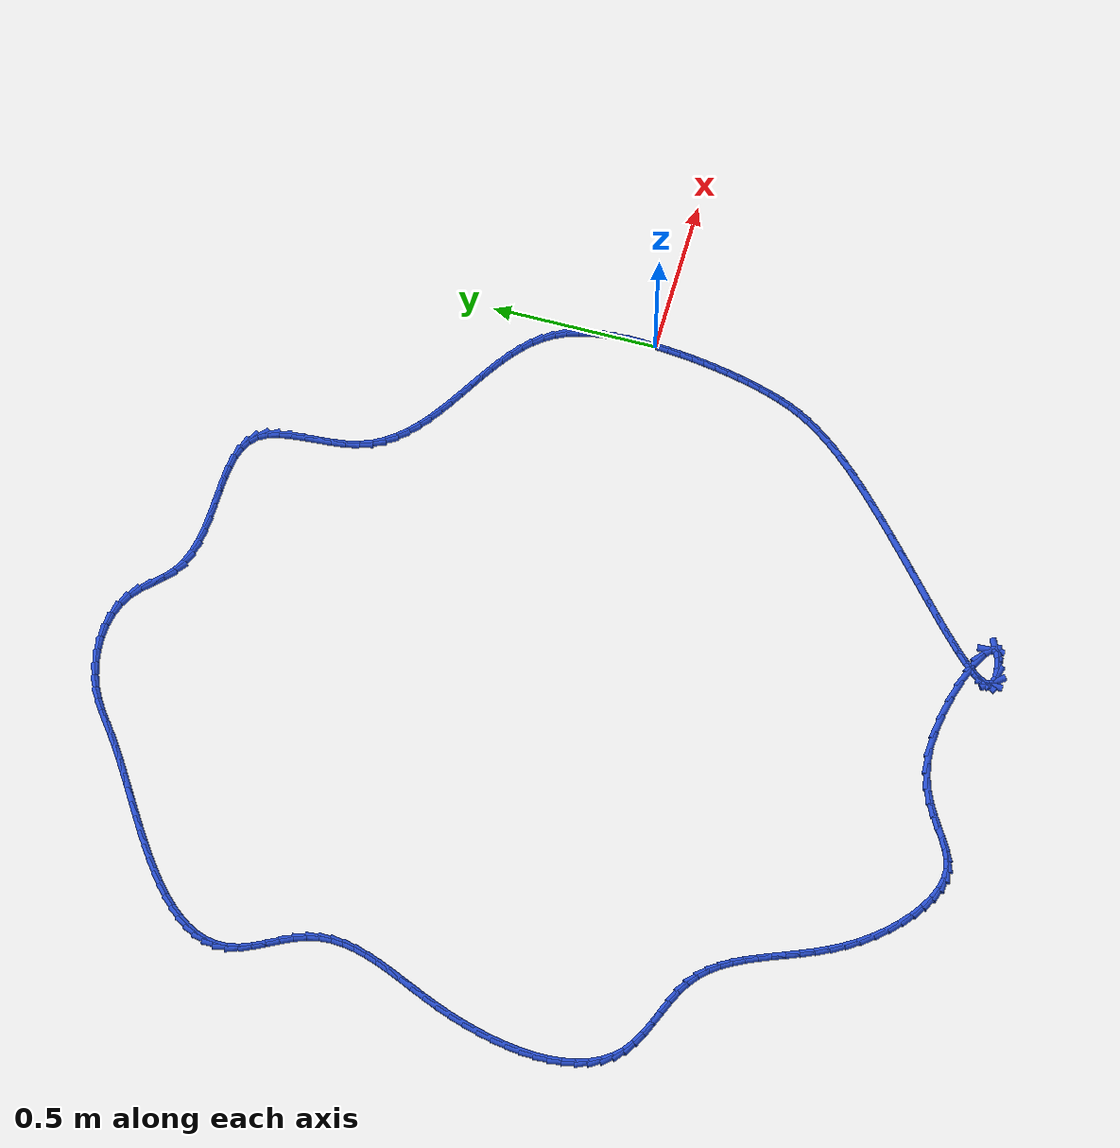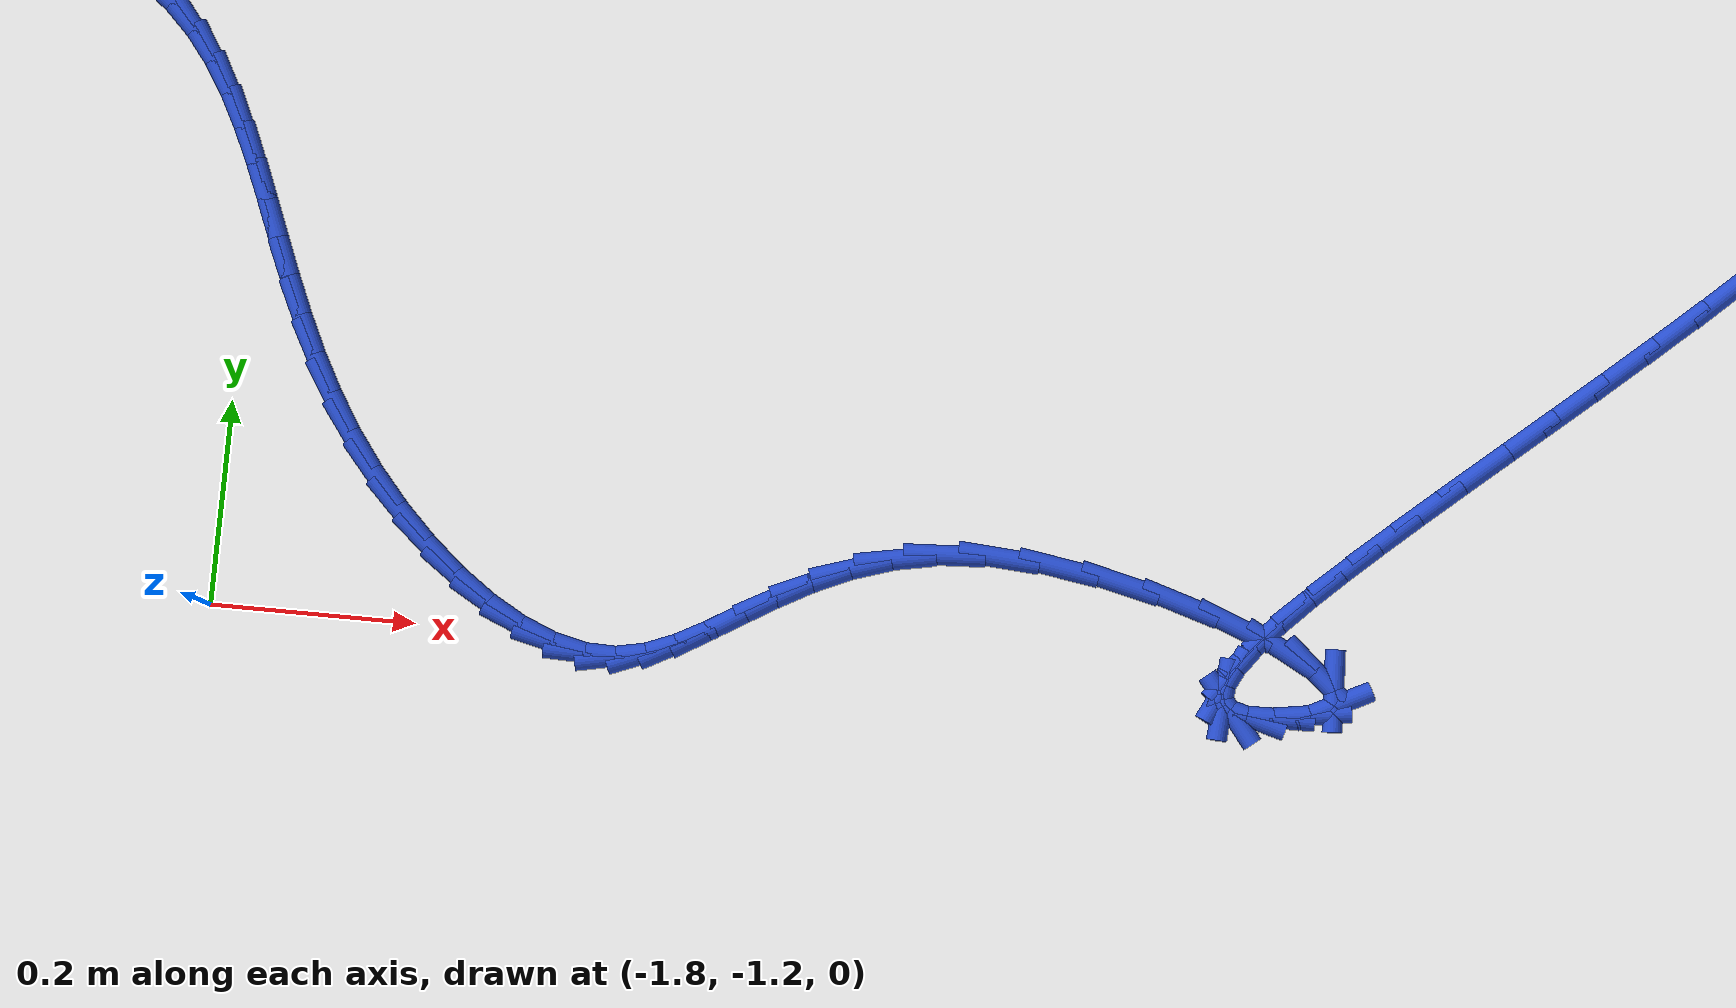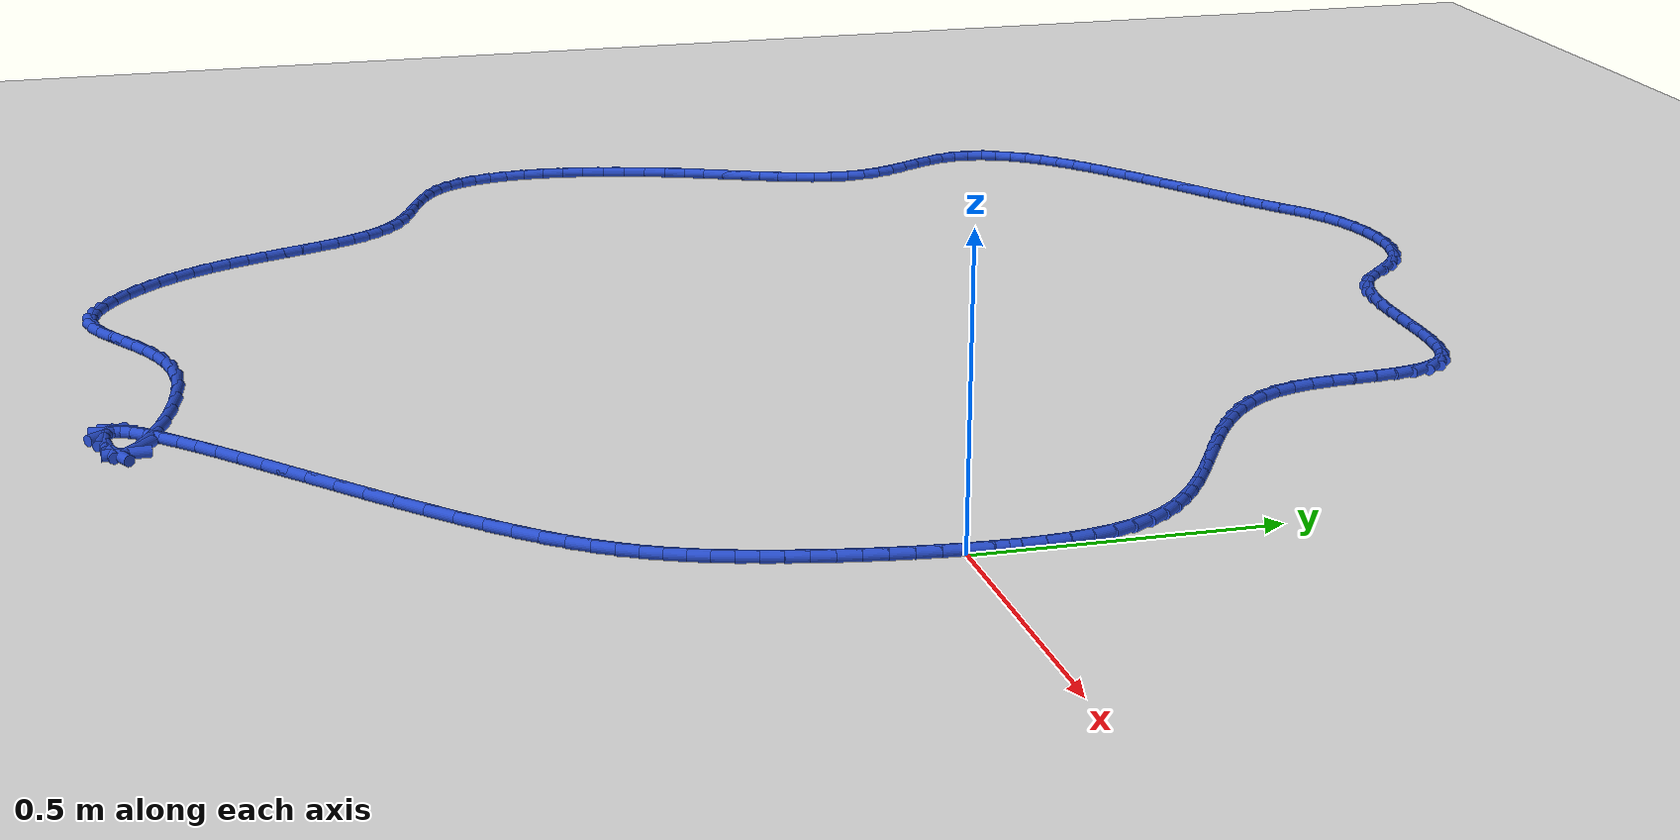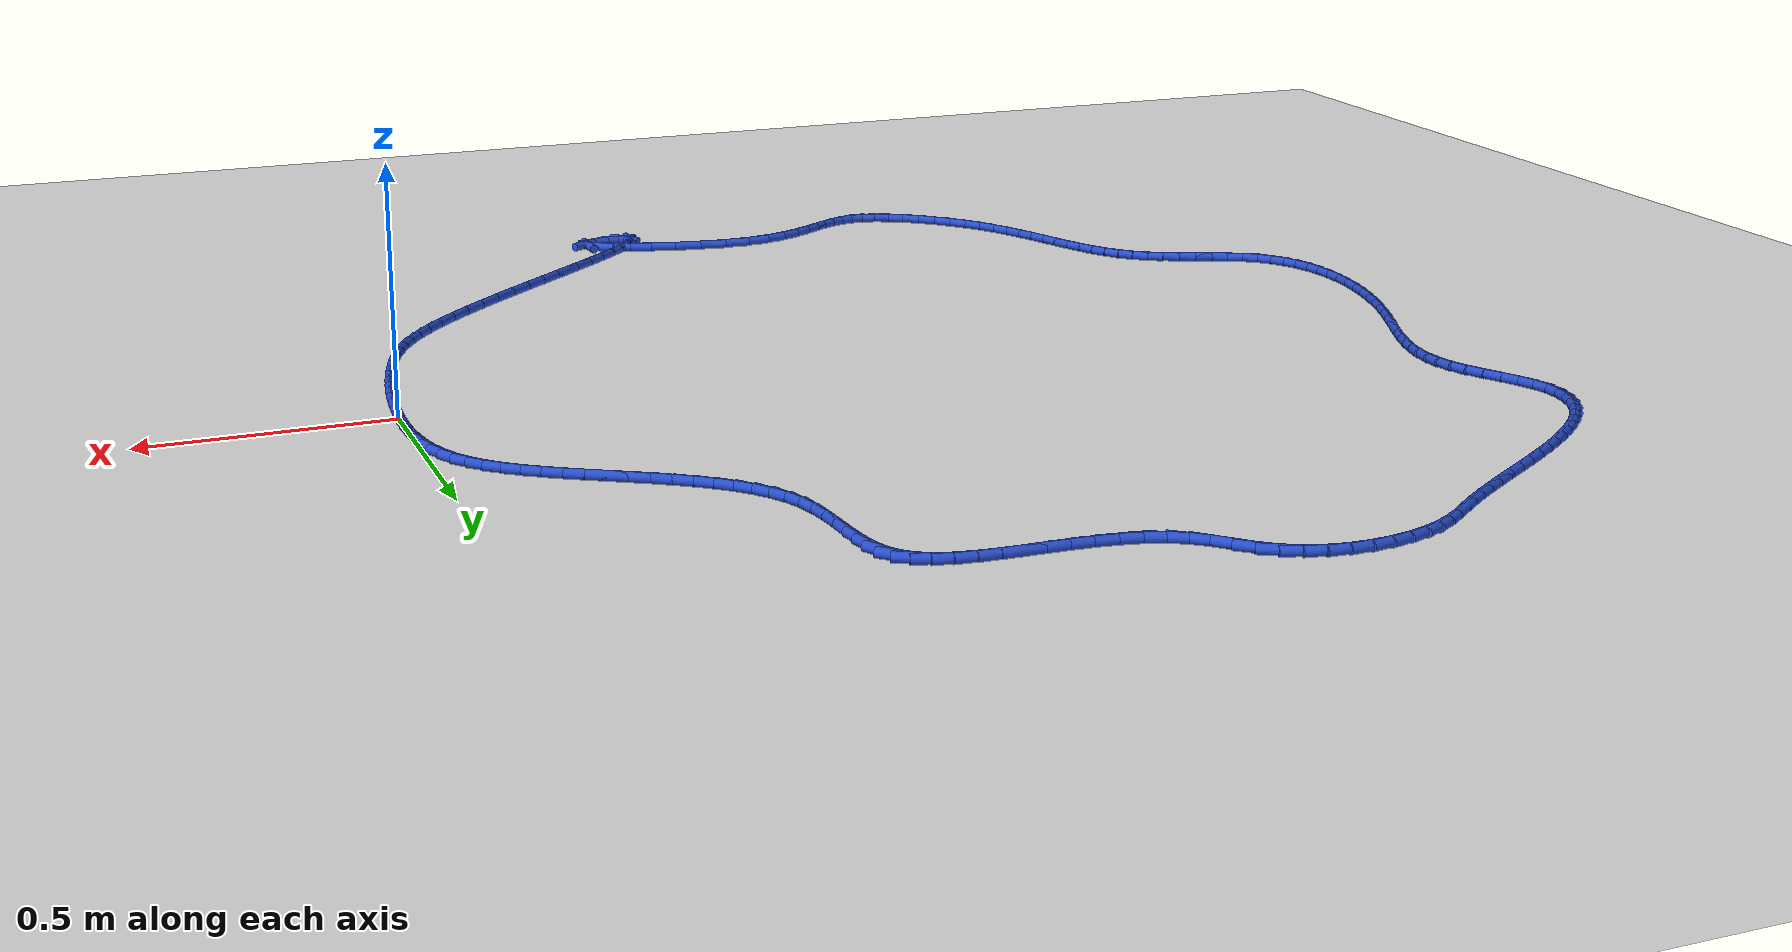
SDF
<sdf version="1.6">
 <world name="default">
  <light name="sun" type="directional">
   <pose>0 0 10 0 -0 0</pose>
   <diffuse>0.8 0.8 0.8 1</diffuse>
   <specular>0.2 0.2 0.2 1</specular>
   <attenuation>
    <range>1000</range>
    <constant>0.9</constant>
    <linear>0.01</linear>
    <quadratic>0.001</quadratic>
   </attenuation>
   <direction>-0.5 0.1 -0.9</direction>
  </light>
  <model name="ground_plane">
   <static>1</static>
   <link name="link">
    <collision name="collision">
     <geometry><plane><normal>0 0 1</normal><size>100 100</size></plane></geometry>
     <surface><friction><ode><mu>100</mu><mu2>50</mu2></ode></friction></surface>
    </collision>
    <visual name="visual">
     <cast_shadows>0</cast_shadows>
     <geometry><plane><normal>0 0 1</normal><size>100 100</size></plane></geometry>
     <material>
      <script><uri>file://media/materials/scripts/gazebo.material</uri><name>Gazebo/WhiteGlow</name></script>
     </material>
    </visual>
   </link>
  </model>
  <gravity>0 0 -9.8</gravity>
  <magnetic_field>6e-06 2.3e-05 -4.2e-05</magnetic_field>
  <atmosphere type="adiabatic"/>
  <physics name="default_physics" default="0" type="ode">
   <max_step_size>0.001</max_step_size>
   <real_time_factor>1</real_time_factor>
   <real_time_update_rate>1000</real_time_update_rate>
  </physics>
  <scene><ambient>0.4 0.4 0.4 1</ambient><background>0.7 0.7 0.7 1</background><shadows>1</shadows></scene>
  <spherical_coordinates>
   <surface_model>EARTH_WGS84</surface_model>
   <latitude_deg>0</latitude_deg>
   <longitude_deg>0</longitude_deg>
   <elevation>0</elevation>
   <heading_deg>0</heading_deg>
  </spherical_coordinates>
  <model name="line">
   <link name="link_0">
    <pose>1.8323016715005025e-17 -6.245004513516506e-17 0.01 0 1.57 1.5251426368215633</pose>
    <collision name="collision">
     <geometry><cylinder><radius>0.01</radius><length>0.08</length></cylinder></geometry>
    </collision>
    <visual name="visual">
     <material>
      <script><name>Gazebo/Blue</name><uri>file://media/materials/scripts/gazebo.material</uri></script>
     </material>
     <geometry><cylinder><radius>0.01</radius><length>0.08</length></cylinder></geometry>
    </visual>
   </link>
   <link name="link_1">
    <pose>0.001823124579597939 0.039906035702922844 0.01 0 1.57 1.5586776729738612</pose>
    <collision name="collision">
     <geometry><cylinder><radius>0.01</radius><length>0.08</length></cylinder></geometry>
    </collision>
    <visual name="visual">
     <material>
      <script><name>Gazebo/Blue</name><uri>file://media/materials/scripts/gazebo.material</uri></script>
     </material>
     <geometry><cylinder><radius>0.01</radius><length>0.08</length></cylinder></geometry>
    </visual>
   </link>
   <link name="link_2">
    <pose>0.002307320925035968 0.07985871106152502 0.01 0 1.57 -1.5397878494639026</pose>
    <collision name="collision">
     <geometry><cylinder><radius>0.01</radius><length>0.08</length></cylinder></geometry>
    </collision>
    <visual name="visual">
     <material>
      <script><name>Gazebo/Blue</name><uri>file://media/materials/scripts/gazebo.material</uri></script>
     </material>
     <geometry><cylinder><radius>0.01</radius><length>0.08</length></cylinder></geometry>
    </visual>
   </link>
   <link name="link_3">
    <pose>0.001077854602514132 0.11949536363447913 0.01 0 1.57 -1.4858361308100432</pose>
    <collision name="collision">
     <geometry><cylinder><radius>0.01</radius><length>0.08</length></cylinder></geometry>
    </collision>
    <visual name="visual">
     <material>
      <script><name>Gazebo/Blue</name><uri>file://media/materials/scripts/gazebo.material</uri></script>
     </material>
     <geometry><cylinder><radius>0.01</radius><length>0.08</length></cylinder></geometry>
    </visual>
   </link>
   <link name="link_4">
    <pose>-0.00224000882176753 0.15845333098045805 0.01 0 1.57 -1.419495529759492</pose>
    <collision name="collision">
     <geometry><cylinder><radius>0.01</radius><length>0.08</length></cylinder></geometry>
    </collision>
    <visual name="visual">
     <material>
      <script><name>Gazebo/Blue</name><uri>file://media/materials/scripts/gazebo.material</uri></script>
     </material>
     <geometry><cylinder><radius>0.01</radius><length>0.08</length></cylinder></geometry>
    </visual>
   </link>
   <link name="link_5">
    <pose>-0.008021003781608981 0.19636995065813442 0.01 0 1.57 -1.3389880088679615</pose>
    <collision name="collision">
     <geometry><cylinder><radius>0.01</radius><length>0.08</length></cylinder></geometry>
    </collision>
    <visual name="visual">
     <material>
      <script><name>Gazebo/Blue</name><uri>file://media/materials/scripts/gazebo.material</uri></script>
     </material>
     <geometry><cylinder><radius>0.01</radius><length>0.08</length></cylinder></geometry>
    </visual>
   </link>
   <link name="link_6">
    <pose>-0.01663986471081019 0.2328825602261812 0.01 0 1.57 -1.2425975833872176</pose>
    <collision name="collision">
     <geometry><cylinder><radius>0.01</radius><length>0.08</length></cylinder></geometry>
    </collision>
    <visual name="visual">
     <material>
      <script><name>Gazebo/Blue</name><uri>file://media/materials/scripts/gazebo.material</uri></script>
     </material>
     <geometry><cylinder><radius>0.01</radius><length>0.08</length></cylinder></geometry>
    </visual>
   </link>
   <link name="link_7">
    <pose>-0.028471326043171135 0.26762849724327115 0.01 0 1.57 -1.1292029909747927</pose>
    <collision name="collision">
     <geometry><cylinder><radius>0.01</radius><length>0.08</length></cylinder></geometry>
    </collision>
    <visual name="visual">
     <material>
      <script><name>Gazebo/Blue</name><uri>file://media/materials/scripts/gazebo.material</uri></script>
     </material>
     <geometry><cylinder><radius>0.01</radius><length>0.08</length></cylinder></geometry>
    </visual>
   </link>
   <link name="link_8">
    <pose>-0.04389012221249174 0.30024509926807685 0.01 0 1.57 -1.0010231774164045</pose>
    <collision name="collision">
     <geometry><cylinder><radius>0.01</radius><length>0.08</length></cylinder></geometry>
    </collision>
    <visual name="visual">
     <material>
      <script><name>Gazebo/Blue</name><uri>file://media/materials/scripts/gazebo.material</uri></script>
     </material>
     <geometry><cylinder><radius>0.01</radius><length>0.08</length></cylinder></geometry>
    </visual>
   </link>
   <link name="link_9">
    <pose>-0.0632168896026896 0.3304126028798858 0.01 0 1.57 -0.8792305918177935</pose>
    <collision name="collision">
     <geometry><cylinder><radius>0.01</radius><length>0.08</length></cylinder></geometry>
    </collision>
    <visual name="visual">
     <material>
      <script><name>Gazebo/Blue</name><uri>file://media/materials/scripts/gazebo.material</uri></script>
     </material>
     <geometry><cylinder><radius>0.01</radius><length>0.08</length></cylinder></geometry>
    </visual>
   </link>
   <link name="link_10">
    <pose>-0.08624703949034289 0.3582277410521449 0.01 0 1.57 -0.7769436868115438</pose>
    <collision name="collision">
     <geometry><cylinder><radius>0.01</radius><length>0.08</length></cylinder></geometry>
    </collision>
    <visual name="visual">
     <material>
      <script><name>Gazebo/Blue</name><uri>file://media/materials/scripts/gazebo.material</uri></script>
     </material>
     <geometry><cylinder><radius>0.01</radius><length>0.08</length></cylinder></geometry>
    </visual>
   </link>
   <link name="link_11">
    <pose>-0.11248063020996737 0.3840214576397958 0.01 0 1.57 -0.6946230285980459</pose>
    <collision name="collision">
     <geometry><cylinder><radius>0.01</radius><length>0.08</length></cylinder></geometry>
    </collision>
    <visual name="visual">
     <material>
      <script><name>Gazebo/Blue</name><uri>file://media/materials/scripts/gazebo.material</uri></script>
     </material>
     <geometry><cylinder><radius>0.01</radius><length>0.08</length></cylinder></geometry>
    </visual>
   </link>
   <link name="link_12">
    <pose>-0.14141442858764197 0.40812730661937613 0.01 0 1.57 -0.6311238713219045</pose>
    <collision name="collision">
     <geometry><cylinder><radius>0.01</radius><length>0.08</length></cylinder></geometry>
    </collision>
    <visual name="visual">
     <material>
      <script><name>Gazebo/Blue</name><uri>file://media/materials/scripts/gazebo.material</uri></script>
     </material>
     <geometry><cylinder><radius>0.01</radius><length>0.08</length></cylinder></geometry>
    </visual>
   </link>
   <link name="link_13">
    <pose>-0.17254520144944543 0.4308788419674236 0.01 0 1.57 -0.5847849378091307</pose>
    <collision name="collision">
     <geometry><cylinder><radius>0.01</radius><length>0.08</length></cylinder></geometry>
    </collision>
    <visual name="visual">
     <material>
      <script><name>Gazebo/Blue</name><uri>file://media/materials/scripts/gazebo.material</uri></script>
     </material>
     <geometry><cylinder><radius>0.01</radius><length>0.08</length></cylinder></geometry>
    </visual>
   </link>
   <link name="link_14">
    <pose>-0.20536971562145648 0.4526096176604761 0.01 0 1.57 -0.5540237378900601</pose>
    <collision name="collision">
     <geometry><cylinder><radius>0.01</radius><length>0.08</length></cylinder></geometry>
    </collision>
    <visual name="visual">
     <material>
      <script><name>Gazebo/Blue</name><uri>file://media/materials/scripts/gazebo.material</uri></script>
     </material>
     <geometry><cylinder><radius>0.01</radius><length>0.08</length></cylinder></geometry>
    </visual>
   </link>
   <link name="link_15">
    <pose>-0.23938473792975384 0.4736531876750713 0.01 0 1.57 -0.5376293861707933</pose>
    <collision name="collision">
     <geometry><cylinder><radius>0.01</radius><length>0.08</length></cylinder></geometry>
    </collision>
    <visual name="visual">
     <material>
      <script><name>Gazebo/Blue</name><uri>file://media/materials/scripts/gazebo.material</uri></script>
     </material>
     <geometry><cylinder><radius>0.01</radius><length>0.08</length></cylinder></geometry>
    </visual>
   </link>
   <link name="link_16">
    <pose>-0.2740870352004164 0.4943431059877467 0.01 0 1.57 -0.5348794290932097</pose>
    <collision name="collision">
     <geometry><cylinder><radius>0.01</radius><length>0.08</length></cylinder></geometry>
    </collision>
    <visual name="visual">
     <material>
      <script><name>Gazebo/Blue</name><uri>file://media/materials/scripts/gazebo.material</uri></script>
     </material>
     <geometry><cylinder><radius>0.01</radius><length>0.08</length></cylinder></geometry>
    </visual>
   </link>
   <link name="link_17">
    <pose>-0.30897337425952276 0.5150129265750402 0.01 0 1.57 -0.5455721922897313</pose>
    <collision name="collision">
     <geometry><cylinder><radius>0.01</radius><length>0.08</length></cylinder></geometry>
    </collision>
    <visual name="visual">
     <material>
      <script><name>Gazebo/Blue</name><uri>file://media/materials/scripts/gazebo.material</uri></script>
     </material>
     <geometry><cylinder><radius>0.01</radius><length>0.08</length></cylinder></geometry>
    </visual>
   </link>
   <link name="link_18">
    <pose>-0.3435405219331518 0.5359962034134895 0.01 0 1.57 -0.5700206003601942</pose>
    <collision name="collision">
     <geometry><cylinder><radius>0.01</radius><length>0.08</length></cylinder></geometry>
    </collision>
    <visual name="visual">
     <material>
      <script><name>Gazebo/Blue</name><uri>file://media/materials/scripts/gazebo.material</uri></script>
     </material>
     <geometry><cylinder><radius>0.01</radius><length>0.08</length></cylinder></geometry>
    </visual>
   </link>
   <link name="link_19">
    <pose>-0.3772852450473824 0.5576264904796324 0.01 0 1.57 -0.609016117247484</pose>
    <collision name="collision">
     <geometry><cylinder><radius>0.01</radius><length>0.08</length></cylinder></geometry>
    </collision>
    <visual name="visual">
     <material>
      <script><name>Gazebo/Blue</name><uri>file://media/materials/scripts/gazebo.material</uri></script>
     </material>
     <geometry><cylinder><radius>0.01</radius><length>0.08</length></cylinder></geometry>
    </visual>
   </link>
   <link name="link_20">
    <pose>-0.40970431042829325 0.5802373417500064 0.01 0 1.57 -0.6637386016183862</pose>
    <collision name="collision">
     <geometry><cylinder><radius>0.01</radius><length>0.08</length></cylinder></geometry>
    </collision>
    <visual name="visual">
     <material>
      <script><name>Gazebo/Blue</name><uri>file://media/materials/scripts/gazebo.material</uri></script>
     </material>
     <geometry><cylinder><radius>0.01</radius><length>0.08</length></cylinder></geometry>
    </visual>
   </link>
   <link name="link_21">
    <pose>-0.4402944849019629 0.6041623112011494 0.01 0 1.57 -0.7355532823651634</pose>
    <collision name="collision">
     <geometry><cylinder><radius>0.01</radius><length>0.08</length></cylinder></geometry>
    </collision>
    <visual name="visual">
     <material>
      <script><name>Gazebo/Blue</name><uri>file://media/materials/scripts/gazebo.material</uri></script>
     </material>
     <geometry><cylinder><radius>0.01</radius><length>0.08</length></cylinder></geometry>
    </visual>
   </link>
   <link name="link_22">
    <pose>-0.4685525352944704 0.6297349528095991 0.01 0 1.57 -0.8256051158203653</pose>
    <collision name="collision">
     <geometry><cylinder><radius>0.01</radius><length>0.08</length></cylinder></geometry>
    </collision>
    <visual name="visual">
     <material>
      <script><name>Gazebo/Blue</name><uri>file://media/materials/scripts/gazebo.material</uri></script>
     </material>
     <geometry><cylinder><radius>0.01</radius><length>0.08</length></cylinder></geometry>
    </visual>
   </link>
   <link name="link_23">
    <pose>-0.49397522843189434 0.657288820551893 0.01 0 1.57 -0.9341305927136866</pose>
    <collision name="collision">
     <geometry><cylinder><radius>0.01</radius><length>0.08</length></cylinder></geometry>
    </collision>
    <visual name="visual">
     <material>
      <script><name>Gazebo/Blue</name><uri>file://media/materials/scripts/gazebo.material</uri></script>
     </material>
     <geometry><cylinder><radius>0.01</radius><length>0.08</length></cylinder></geometry>
    </visual>
   </link>
   <link name="link_24">
    <pose>-0.5160593311403135 0.687157468404569 0.01 0 1.57 -1.0595411625086781</pose>
    <collision name="collision">
     <geometry><cylinder><radius>0.01</radius><length>0.08</length></cylinder></geometry>
    </collision>
    <visual name="visual">
     <material>
      <script><name>Gazebo/Blue</name><uri>file://media/materials/scripts/gazebo.material</uri></script>
     </material>
     <geometry><cylinder><radius>0.01</radius><length>0.08</length></cylinder></geometry>
    </visual>
   </link>
   <link name="link_25">
    <pose>-0.534301610245807 0.7196744503441652 0.01 0 1.57 -1.1976532402411308</pose>
    <collision name="collision">
     <geometry><cylinder><radius>0.01</radius><length>0.08</length></cylinder></geometry>
    </collision>
    <visual name="visual">
     <material>
      <script><name>Gazebo/Blue</name><uri>file://media/materials/scripts/gazebo.material</uri></script>
     </material>
     <geometry><cylinder><radius>0.01</radius><length>0.08</length></cylinder></geometry>
    </visual>
   </link>
   <link name="link_26">
    <pose>-0.5481988325744529 0.7551733203472184 0.01 0 1.57 -1.3338044163054625</pose>
    <collision name="collision">
     <geometry><cylinder><radius>0.01</radius><length>0.08</length></cylinder></geometry>
    </collision>
    <visual name="visual">
     <material>
      <script><name>Gazebo/Blue</name><uri>file://media/materials/scripts/gazebo.material</uri></script>
     </material>
     <geometry><cylinder><radius>0.01</radius><length>0.08</length></cylinder></geometry>
    </visual>
   </link>
   <link name="link_27">
    <pose>-0.5575195143480137 0.7937633534116468 0.01 0 1.57 -1.429081332650051</pose>
    <collision name="collision">
     <geometry><cylinder><radius>0.01</radius><length>0.08</length></cylinder></geometry>
    </collision>
    <visual name="visual">
     <material>
      <script><name>Gazebo/Blue</name><uri>file://media/materials/scripts/gazebo.material</uri></script>
     </material>
     <geometry><cylinder><radius>0.01</radius><length>0.08</length></cylinder></geometry>
    </visual>
   </link>
   <link name="link_28">
    <pose>-0.5633291056641021 0.8344834449516989 0.01 0 1.57 -1.4808205636777063</pose>
    <collision name="collision">
     <geometry><cylinder><radius>0.01</radius><length>0.08</length></cylinder></geometry>
    </collision>
    <visual name="visual">
     <material>
      <script><name>Gazebo/Blue</name><uri>file://media/materials/scripts/gazebo.material</uri></script>
     </material>
     <geometry><cylinder><radius>0.01</radius><length>0.08</length></cylinder></geometry>
    </visual>
   </link>
   <link name="link_29">
    <pose>-0.5670795316438053 0.8760535265682564 0.01 0 1.57 -1.4945405960229985</pose>
    <collision name="collision">
     <geometry><cylinder><radius>0.01</radius><length>0.08</length></cylinder></geometry>
    </collision>
    <visual name="visual">
     <material>
      <script><name>Gazebo/Blue</name><uri>file://media/materials/scripts/gazebo.material</uri></script>
     </material>
     <geometry><cylinder><radius>0.01</radius><length>0.08</length></cylinder></geometry>
    </visual>
   </link>
   <link name="link_30">
    <pose>-0.5702227834678856 0.9171934753421302 0.01 0 1.57 -1.4699953311609737</pose>
    <collision name="collision">
     <geometry><cylinder><radius>0.01</radius><length>0.08</length></cylinder></geometry>
    </collision>
    <visual name="visual">
     <material>
      <script><name>Gazebo/Blue</name><uri>file://media/materials/scripts/gazebo.material</uri></script>
     </material>
     <geometry><cylinder><radius>0.01</radius><length>0.08</length></cylinder></geometry>
    </visual>
   </link>
   <link name="link_31">
    <pose>-0.574210852317106 0.9566231683541315 0.01 0 1.57 -1.4000015076557584</pose>
    <collision name="collision">
     <geometry><cylinder><radius>0.01</radius><length>0.08</length></cylinder></geometry>
    </collision>
    <visual name="visual">
     <material>
      <script><name>Gazebo/Blue</name><uri>file://media/materials/scripts/gazebo.material</uri></script>
     </material>
     <geometry><cylinder><radius>0.01</radius><length>0.08</length></cylinder></geometry>
    </visual>
   </link>
   <link name="link_32">
    <pose>-0.5804957293722287 0.9930624826850704 0.01 0 1.57 -1.2684518321111597</pose>
    <collision name="collision">
     <geometry><cylinder><radius>0.01</radius><length>0.08</length></cylinder></geometry>
    </collision>
    <visual name="visual">
     <material>
      <script><name>Gazebo/Blue</name><uri>file://media/materials/scripts/gazebo.material</uri></script>
     </material>
     <geometry><cylinder><radius>0.01</radius><length>0.08</length></cylinder></geometry>
    </visual>
   </link>
   <link name="link_33">
    <pose>-0.5905294058140163 1.0252312954157574 0.01 0 1.57 -1.050968693917539</pose>
    <collision name="collision">
     <geometry><cylinder><radius>0.01</radius><length>0.08</length></cylinder></geometry>
    </collision>
    <visual name="visual">
     <material>
      <script><name>Gazebo/Blue</name><uri>file://media/materials/scripts/gazebo.material</uri></script>
     </material>
     <geometry><cylinder><radius>0.01</radius><length>0.08</length></cylinder></geometry>
    </visual>
   </link>
   <link name="link_34">
    <pose>-0.6057638727901493 1.0518494836597798 0.01 0 1.57 -0.7537559444594807</pose>
    <collision name="collision">
     <geometry><cylinder><radius>0.01</radius><length>0.08</length></cylinder></geometry>
    </collision>
    <visual name="visual">
     <material>
      <script><name>Gazebo/Blue</name><uri>file://media/materials/scripts/gazebo.material</uri></script>
     </material>
     <geometry><cylinder><radius>0.01</radius><length>0.08</length></cylinder></geometry>
    </visual>
   </link>
   <link name="link_35">
    <pose>-0.6272589074992032 1.0720255131921494 0.01 0 1.57 -0.48520055452709066</pose>
    <collision name="collision">
     <geometry><cylinder><radius>0.01</radius><length>0.08</length></cylinder></geometry>
    </collision>
    <visual name="visual">
     <material>
      <script><name>Gazebo/Blue</name><uri>file://media/materials/scripts/gazebo.material</uri></script>
     </material>
     <geometry><cylinder><radius>0.01</radius><length>0.08</length></cylinder></geometry>
    </visual>
   </link>
   <link name="link_36">
    <pose>-0.6545260261993893 1.0864017999386189 0.01 0 1.57 -0.28993866395748036</pose>
    <collision name="collision">
     <geometry><cylinder><radius>0.01</radius><length>0.08</length></cylinder></geometry>
    </collision>
    <visual name="visual">
     <material>
      <script><name>Gazebo/Blue</name><uri>file://media/materials/scripts/gazebo.material</uri></script>
     </material>
     <geometry><cylinder><radius>0.01</radius><length>0.08</length></cylinder></geometry>
    </visual>
   </link>
   <link name="link_37">
    <pose>-0.6866947612168182 1.0959992130268215 0.01 0 1.57 -0.15993244494692524</pose>
    <collision name="collision">
     <geometry><cylinder><radius>0.01</radius><length>0.08</length></cylinder></geometry>
    </collision>
    <visual name="visual">
     <material>
      <script><name>Gazebo/Blue</name><uri>file://media/materials/scripts/gazebo.material</uri></script>
     </material>
     <geometry><cylinder><radius>0.01</radius><length>0.08</length></cylinder></geometry>
    </visual>
   </link>
   <link name="link_38">
    <pose>-0.7228946448776001 1.1018386215843894 0.01 0 1.57 -0.07865418494785999</pose>
    <collision name="collision">
     <geometry><cylinder><radius>0.01</radius><length>0.08</length></cylinder></geometry>
    </collision>
    <visual name="visual">
     <material>
      <script><name>Gazebo/Blue</name><uri>file://media/materials/scripts/gazebo.material</uri></script>
     </material>
     <geometry><cylinder><radius>0.01</radius><length>0.08</length></cylinder></geometry>
    </visual>
   </link>
   <link name="link_39">
    <pose>-0.7622552095078462 1.1049408947389567 0.01 0 1.57 -0.03326457967982787</pose>
    <collision name="collision">
     <geometry><cylinder><radius>0.01</radius><length>0.08</length></cylinder></geometry>
    </collision>
    <visual name="visual">
     <material>
      <script><name>Gazebo/Blue</name><uri>file://media/materials/scripts/gazebo.material</uri></script>
     </material>
     <geometry><cylinder><radius>0.01</radius><length>0.08</length></cylinder></geometry>
    </visual>
   </link>
   <link name="link_40">
    <pose>-0.8039059874336666 1.1063269016181552 0.01 0 1.57 -0.016033019755761532</pose>
    <collision name="collision">
     <geometry><cylinder><radius>0.01</radius><length>0.08</length></cylinder></geometry>
    </collision>
    <visual name="visual">
     <material>
      <script><name>Gazebo/Blue</name><uri>file://media/materials/scripts/gazebo.material</uri></script>
     </material>
     <geometry><cylinder><radius>0.01</radius><length>0.08</length></cylinder></geometry>
    </visual>
   </link>
   <link name="link_41">
    <pose>-0.8469765109811722 1.107017511349619 0.01 0 1.57 -0.02328983527560431</pose>
    <collision name="collision">
     <geometry><cylinder><radius>0.01</radius><length>0.08</length></cylinder></geometry>
    </collision>
    <visual name="visual">
     <material>
      <script><name>Gazebo/Blue</name><uri>file://media/materials/scripts/gazebo.material</uri></script>
     </material>
     <geometry><cylinder><radius>0.01</radius><length>0.08</length></cylinder></geometry>
    </visual>
   </link>
   <link name="link_42">
    <pose>-0.8905963124764729 1.10803359306098 0.01 0 1.57 -0.0545071227931447</pose>
    <collision name="collision">
     <geometry><cylinder><radius>0.01</radius><length>0.08</length></cylinder></geometry>
    </collision>
    <visual name="visual">
     <material>
      <script><name>Gazebo/Blue</name><uri>file://media/materials/scripts/gazebo.material</uri></script>
     </material>
     <geometry><cylinder><radius>0.01</radius><length>0.08</length></cylinder></geometry>
    </visual>
   </link>
   <link name="link_43">
    <pose>-0.9338949242456803 1.1103960158798722 0.01 0 1.57 -0.11185542867054082</pose>
    <collision name="collision">
     <geometry><cylinder><radius>0.01</radius><length>0.08</length></cylinder></geometry>
    </collision>
    <visual name="visual">
     <material>
      <script><name>Gazebo/Blue</name><uri>file://media/materials/scripts/gazebo.material</uri></script>
     </material>
     <geometry><cylinder><radius>0.01</radius><length>0.08</length></cylinder></geometry>
    </visual>
   </link>
   <link name="link_44">
    <pose>-0.9760018786149042 1.1151256489339276 0.01 0 1.57 -0.20000536451096976</pose>
    <collision name="collision">
     <geometry><cylinder><radius>0.01</radius><length>0.08</length></cylinder></geometry>
    </collision>
    <visual name="visual">
     <material>
      <script><name>Gazebo/Blue</name><uri>file://media/materials/scripts/gazebo.material</uri></script>
     </material>
     <geometry><cylinder><radius>0.01</radius><length>0.08</length></cylinder></geometry>
    </visual>
   </link>
   <link name="link_45">
    <pose>-1.0160467079102555 1.12324336135078 0.01 0 1.57 -0.32552684393863046</pose>
    <collision name="collision">
     <geometry><cylinder><radius>0.01</radius><length>0.08</length></cylinder></geometry>
    </collision>
    <visual name="visual">
     <material>
      <script><name>Gazebo/Blue</name><uri>file://media/materials/scripts/gazebo.material</uri></script>
     </material>
     <geometry><cylinder><radius>0.01</radius><length>0.08</length></cylinder></geometry>
    </visual>
   </link>
   <link name="link_46">
    <pose>-1.0531589444578446 1.1357700222580616 0.01 0 1.57 -0.4944245993701567</pose>
    <collision name="collision">
     <geometry><cylinder><radius>0.01</radius><length>0.08</length></cylinder></geometry>
    </collision>
    <visual name="visual">
     <material>
      <script><name>Gazebo/Blue</name><uri>file://media/materials/scripts/gazebo.material</uri></script>
     </material>
     <geometry><cylinder><radius>0.01</radius><length>0.08</length></cylinder></geometry>
    </visual>
   </link>
   <link name="link_47">
    <pose>-1.086468120583782 1.1537265007834059 0.01 0 1.57 -0.6862244633565404</pose>
    <collision name="collision">
     <geometry><cylinder><radius>0.01</radius><length>0.08</length></cylinder></geometry>
    </collision>
    <visual name="visual">
     <material>
      <script><name>Gazebo/Blue</name><uri>file://media/materials/scripts/gazebo.material</uri></script>
     </material>
     <geometry><cylinder><radius>0.01</radius><length>0.08</length></cylinder></geometry>
    </visual>
   </link>
   <link name="link_48">
    <pose>-1.1155477952525485 1.1775429996897178 0.01 0 1.57 -0.794600883487039</pose>
    <collision name="collision">
     <geometry><cylinder><radius>0.01</radius><length>0.08</length></cylinder></geometry>
    </collision>
    <visual name="visual">
     <material>
      <script><name>Gazebo/Blue</name><uri>file://media/materials/scripts/gazebo.material</uri></script>
     </material>
     <geometry><cylinder><radius>0.01</radius><length>0.08</length></cylinder></geometry>
    </visual>
   </link>
   <link name="link_49">
    <pose>-1.1421978610895869 1.204688141743224 0.01 0 1.57 -0.7909723684042106</pose>
    <collision name="collision">
     <geometry><cylinder><radius>0.01</radius><length>0.08</length></cylinder></geometry>
    </collision>
    <visual name="visual">
     <material>
      <script><name>Gazebo/Blue</name><uri>file://media/materials/scripts/gazebo.material</uri></script>
     </material>
     <geometry><cylinder><radius>0.01</radius><length>0.08</length></cylinder></geometry>
    </visual>
   </link>
   <link name="link_50">
    <pose>-1.168914504107076 1.2317043055437247 0.01 0 1.57 -0.675244704111775</pose>
    <collision name="collision">
     <geometry><cylinder><radius>0.01</radius><length>0.08</length></cylinder></geometry>
    </collision>
    <visual name="visual">
     <material>
      <script><name>Gazebo/Blue</name><uri>file://media/materials/scripts/gazebo.material</uri></script>
     </material>
     <geometry><cylinder><radius>0.01</radius><length>0.08</length></cylinder></geometry>
    </visual>
   </link>
   <link name="link_51">
    <pose>-1.1981844082858912 1.255144420540293 0.01 0 1.57 -0.48816108888344306</pose>
    <collision name="collision">
     <geometry><cylinder><radius>0.01</radius><length>0.08</length></cylinder></geometry>
    </collision>
    <visual name="visual">
     <material>
      <script><name>Gazebo/Blue</name><uri>file://media/materials/scripts/gazebo.material</uri></script>
     </material>
     <geometry><cylinder><radius>0.01</radius><length>0.08</length></cylinder></geometry>
    </visual>
   </link>
   <link name="link_52">
    <pose>-1.2313996828388218 1.272782673707708 0.01 0 1.57 -0.31623301540688836</pose>
    <collision name="collision">
     <geometry><cylinder><radius>0.01</radius><length>0.08</length></cylinder></geometry>
    </collision>
    <visual name="visual">
     <material>
      <script><name>Gazebo/Blue</name><uri>file://media/materials/scripts/gazebo.material</uri></script>
     </material>
     <geometry><cylinder><radius>0.01</radius><length>0.08</length></cylinder></geometry>
    </visual>
   </link>
   <link name="link_53">
    <pose>-1.2678703011335437 1.2847163679416875 0.01 0 1.57 -0.16814495296478454</pose>
    <collision name="collision">
     <geometry><cylinder><radius>0.01</radius><length>0.08</length></cylinder></geometry>
    </collision>
    <visual name="visual">
     <material>
      <script><name>Gazebo/Blue</name><uri>file://media/materials/scripts/gazebo.material</uri></script>
     </material>
     <geometry><cylinder><radius>0.01</radius><length>0.08</length></cylinder></geometry>
    </visual>
   </link>
   <link name="link_54">
    <pose>-1.3066729993485175 1.2913030374907157 0.01 0 1.57 -0.039698579184489505</pose>
    <collision name="collision">
     <geometry><cylinder><radius>0.01</radius><length>0.08</length></cylinder></geometry>
    </collision>
    <visual name="visual">
     <material>
      <script><name>Gazebo/Blue</name><uri>file://media/materials/scripts/gazebo.material</uri></script>
     </material>
     <geometry><cylinder><radius>0.01</radius><length>0.08</length></cylinder></geometry>
    </visual>
   </link>
   <link name="link_55">
    <pose>-1.3468845136622034 1.2929002166032757 0.01 0 1.57 0.07443216153174423</pose>
    <collision name="collision">
     <geometry><cylinder><radius>0.01</radius><length>0.08</length></cylinder></geometry>
    </collision>
    <visual name="visual">
     <material>
      <script><name>Gazebo/Blue</name><uri>file://media/materials/scripts/gazebo.material</uri></script>
     </material>
     <geometry><cylinder><radius>0.01</radius><length>0.08</length></cylinder></geometry>
    </visual>
   </link>
   <link name="link_56">
    <pose>-1.3875815802530633 1.289865439527852 0.01 0 1.57 0.1795966073375467</pose>
    <collision name="collision">
     <geometry><cylinder><radius>0.01</radius><length>0.08</length></cylinder></geometry>
    </collision>
    <visual name="visual">
     <material>
      <script><name>Gazebo/Blue</name><uri>file://media/materials/scripts/gazebo.material</uri></script>
     </material>
     <geometry><cylinder><radius>0.01</radius><length>0.08</length></cylinder></geometry>
    </visual>
   </link>
   <link name="link_57">
    <pose>-1.4278409352995571 1.282556240512927 0.01 0 1.57 0.2809658851779167</pose>
    <collision name="collision">
     <geometry><cylinder><radius>0.01</radius><length>0.08</length></cylinder></geometry>
    </collision>
    <visual name="visual">
     <material>
      <script><name>Gazebo/Blue</name><uri>file://media/materials/scripts/gazebo.material</uri></script>
     </material>
     <geometry><cylinder><radius>0.01</radius><length>0.08</length></cylinder></geometry>
    </visual>
   </link>
   <link name="link_58">
    <pose>-1.466739314980146 1.2713301538069857 0.01 0 1.57 0.38379320949071705</pose>
    <collision name="collision">
     <geometry><cylinder><radius>0.01</radius><length>0.08</length></cylinder></geometry>
    </collision>
    <visual name="visual">
     <material>
      <script><name>Gazebo/Blue</name><uri>file://media/materials/scripts/gazebo.material</uri></script>
     </material>
     <geometry><cylinder><radius>0.01</radius><length>0.08</length></cylinder></geometry>
    </visual>
   </link>
   <link name="link_59">
    <pose>-1.5033534554732912 1.256544713658511 0.01 0 1.57 0.49211683239694737</pose>
    <collision name="collision">
     <geometry><cylinder><radius>0.01</radius><length>0.08</length></cylinder></geometry>
    </collision>
    <visual name="visual">
     <material>
      <script><name>Gazebo/Blue</name><uri>file://media/materials/scripts/gazebo.material</uri></script>
     </material>
     <geometry><cylinder><radius>0.01</radius><length>0.08</length></cylinder></geometry>
    </visual>
   </link>
   <link name="link_60">
    <pose>-1.536870098872072 1.2385760958555416 0.01 0 1.57 0.5849647606834006</pose>
    <collision name="collision">
     <geometry><cylinder><radius>0.01</radius><length>0.08</length></cylinder></geometry>
    </collision>
    <visual name="visual">
     <material>
      <script><name>Gazebo/Blue</name><uri>file://media/materials/scripts/gazebo.material</uri></script>
     </material>
     <geometry><cylinder><radius>0.01</radius><length>0.08</length></cylinder></geometry>
    </visual>
   </link>
   <link name="link_61">
    <pose>-1.567880271418375 1.2180384453770978 0.01 0 1.57 0.6388057241372667</pose>
    <collision name="collision">
     <geometry><cylinder><radius>0.01</radius><length>0.08</length></cylinder></geometry>
    </collision>
    <visual name="visual">
     <material>
      <script><name>Gazebo/Blue</name><uri>file://media/materials/scripts/gazebo.material</uri></script>
     </material>
     <geometry><cylinder><radius>0.01</radius><length>0.08</length></cylinder></geometry>
    </visual>
   </link>
   <link name="link_62">
    <pose>-1.5979443582272108 1.195710174204008 0.01 0 1.57 0.650015130184485</pose>
    <collision name="collision">
     <geometry><cylinder><radius>0.01</radius><length>0.08</length></cylinder></geometry>
    </collision>
    <visual name="visual">
     <material>
      <script><name>Gazebo/Blue</name><uri>file://media/materials/scripts/gazebo.material</uri></script>
     </material>
     <geometry><cylinder><radius>0.01</radius><length>0.08</length></cylinder></geometry>
    </visual>
   </link>
   <link name="link_63">
    <pose>-1.6286420017652314 1.1723729576569268 0.01 0 1.57 0.6257677494787998</pose>
    <collision name="collision">
     <geometry><cylinder><radius>0.01</radius><length>0.08</length></cylinder></geometry>
    </collision>
    <visual name="visual">
     <material>
      <script><name>Gazebo/Blue</name><uri>file://media/materials/scripts/gazebo.material</uri></script>
     </material>
     <geometry><cylinder><radius>0.01</radius><length>0.08</length></cylinder></geometry>
    </visual>
   </link>
   <link name="link_64">
    <pose>-1.6613583724822107 1.1487303911608941 0.01 0 1.57 0.5991002757055448</pose>
    <collision name="collision">
     <geometry><cylinder><radius>0.01</radius><length>0.08</length></cylinder></geometry>
    </collision>
    <visual name="visual">
     <material>
      <script><name>Gazebo/Blue</name><uri>file://media/materials/scripts/gazebo.material</uri></script>
     </material>
     <geometry><cylinder><radius>0.01</radius><length>0.08</length></cylinder></geometry>
    </visual>
   </link>
   <link name="link_65">
    <pose>-1.696169790203636 1.1249605707824295 0.01 0 1.57 0.5811417595870895</pose>
    <collision name="collision">
     <geometry><cylinder><radius>0.01</radius><length>0.08</length></cylinder></geometry>
    </collision>
    <visual name="visual">
     <material>
      <script><name>Gazebo/Blue</name><uri>file://media/materials/scripts/gazebo.material</uri></script>
     </material>
     <geometry><cylinder><radius>0.01</radius><length>0.08</length></cylinder></geometry>
    </visual>
   </link>
   <link name="link_66">
    <pose>-1.7326126786650409 1.1010248260268634 0.01 0 1.57 0.5706550872841195</pose>
    <collision name="collision">
     <geometry><cylinder><radius>0.01</radius><length>0.08</length></cylinder></geometry>
    </collision>
    <visual name="visual">
     <material>
      <script><name>Gazebo/Blue</name><uri>file://media/materials/scripts/gazebo.material</uri></script>
     </material>
     <geometry><cylinder><radius>0.01</radius><length>0.08</length></cylinder></geometry>
    </visual>
   </link>
   <link name="link_67">
    <pose>-1.7702217701656295 1.076883807293224 0.01 0 1.57 0.566850609818267</pose>
    <collision name="collision">
     <geometry><cylinder><radius>0.01</radius><length>0.08</length></cylinder></geometry>
    </collision>
    <visual name="visual">
     <material>
      <script><name>Gazebo/Blue</name><uri>file://media/materials/scripts/gazebo.material</uri></script>
     </material>
     <geometry><cylinder><radius>0.01</radius><length>0.08</length></cylinder></geometry>
    </visual>
   </link>
   <link name="link_68">
    <pose>-1.8085317970046058 1.0524981649805407 0.01 0 1.57 0.5693200197162587</pose>
    <collision name="collision">
     <geometry><cylinder><radius>0.01</radius><length>0.08</length></cylinder></geometry>
    </collision>
    <visual name="visual">
     <material>
      <script><name>Gazebo/Blue</name><uri>file://media/materials/scripts/gazebo.material</uri></script>
     </material>
     <geometry><cylinder><radius>0.01</radius><length>0.08</length></cylinder></geometry>
    </visual>
   </link>
   <link name="link_69">
    <pose>-1.8470774914811734 1.0278285494878414 0.01 0 1.57 0.5779784907206069</pose>
    <collision name="collision">
     <geometry><cylinder><radius>0.01</radius><length>0.08</length></cylinder></geometry>
    </collision>
    <visual name="visual">
     <material>
      <script><name>Gazebo/Blue</name><uri>file://media/materials/scripts/gazebo.material</uri></script>
     </material>
     <geometry><cylinder><radius>0.01</radius><length>0.08</length></cylinder></geometry>
    </visual>
   </link>
   <link name="link_70">
    <pose>-1.885393585894537 1.002835611214156 0.01 0 1.57 0.593042323470632</pose>
    <collision name="collision">
     <geometry><cylinder><radius>0.01</radius><length>0.08</length></cylinder></geometry>
    </collision>
    <visual name="visual">
     <material>
      <script><name>Gazebo/Blue</name><uri>file://media/materials/scripts/gazebo.material</uri></script>
     </material>
     <geometry><cylinder><radius>0.01</radius><length>0.08</length></cylinder></geometry>
    </visual>
   </link>
   <link name="link_71">
    <pose>-1.9230148125438993 0.9774800005585128 0.01 0 1.57 0.6150361345860085</pose>
    <collision name="collision">
     <geometry><cylinder><radius>0.01</radius><length>0.08</length></cylinder></geometry>
    </collision>
    <visual name="visual">
     <material>
      <script><name>Gazebo/Blue</name><uri>file://media/materials/scripts/gazebo.material</uri></script>
     </material>
     <geometry><cylinder><radius>0.01</radius><length>0.08</length></cylinder></geometry>
    </visual>
   </link>
   <link name="link_72">
    <pose>-1.959475903728466 0.9517223679199402 0.01 0 1.57 0.6448269460676399</pose>
    <collision name="collision">
     <geometry><cylinder><radius>0.01</radius><length>0.08</length></cylinder></geometry>
    </collision>
    <visual name="visual">
     <material>
      <script><name>Gazebo/Blue</name><uri>file://media/materials/scripts/gazebo.material</uri></script>
     </material>
     <geometry><cylinder><radius>0.01</radius><length>0.08</length></cylinder></geometry>
    </visual>
   </link>
   <link name="link_73">
    <pose>-1.9943115917474394 0.925523363697467 0.01 0 1.57 0.6836836219163933</pose>
    <collision name="collision">
     <geometry><cylinder><radius>0.01</radius><length>0.08</length></cylinder></geometry>
    </collision>
    <visual name="visual">
     <material>
      <script><name>Gazebo/Blue</name><uri>file://media/materials/scripts/gazebo.material</uri></script>
     </material>
     <geometry><cylinder><radius>0.01</radius><length>0.08</length></cylinder></geometry>
    </visual>
   </link>
   <link name="link_74">
    <pose>-2.0270566089000255 0.8988436382901224 0.01 0 1.57 0.7333570089046385</pose>
    <collision name="collision">
     <geometry><cylinder><radius>0.01</radius><length>0.08</length></cylinder></geometry>
    </collision>
    <visual name="visual">
     <material>
      <script><name>Gazebo/Blue</name><uri>file://media/materials/scripts/gazebo.material</uri></script>
     </material>
     <geometry><cylinder><radius>0.01</radius><length>0.08</length></cylinder></geometry>
    </visual>
   </link>
   <link name="link_75">
    <pose>-2.057245687485426 0.8716438420969348 0.01 0 1.57 0.7961637333405819</pose>
    <collision name="collision">
     <geometry><cylinder><radius>0.01</radius><length>0.08</length></cylinder></geometry>
    </collision>
    <visual name="visual">
     <material>
      <script><name>Gazebo/Blue</name><uri>file://media/materials/scripts/gazebo.material</uri></script>
     </material>
     <geometry><cylinder><radius>0.01</radius><length>0.08</length></cylinder></geometry>
    </visual>
   </link>
   <link name="link_76">
    <pose>-2.0844135598028464 0.8438846255169334 0.01 0 1.57 0.8750237339570035</pose>
    <collision name="collision">
     <geometry><cylinder><radius>0.01</radius><length>0.08</length></cylinder></geometry>
    </collision>
    <visual name="visual">
     <material>
      <script><name>Gazebo/Blue</name><uri>file://media/materials/scripts/gazebo.material</uri></script>
     </material>
     <geometry><cylinder><radius>0.01</radius><length>0.08</length></cylinder></geometry>
    </visual>
   </link>
   <link name="link_77">
    <pose>-2.1080949581514905 0.8155266389491466 0.01 0 1.57 0.9733295523869675</pose>
    <collision name="collision">
     <geometry><cylinder><radius>0.01</radius><length>0.08</length></cylinder></geometry>
    </collision>
    <visual name="visual">
     <material>
      <script><name>Gazebo/Blue</name><uri>file://media/materials/scripts/gazebo.material</uri></script>
     </material>
     <geometry><cylinder><radius>0.01</radius><length>0.08</length></cylinder></geometry>
    </visual>
   </link>
   <link name="link_78">
    <pose>-2.127824614830562 0.7865305327926031 0.01 0 1.57 1.0944019953105522</pose>
    <collision name="collision">
     <geometry><cylinder><radius>0.01</radius><length>0.08</length></cylinder></geometry>
    </collision>
    <visual name="visual">
     <material>
      <script><name>Gazebo/Blue</name><uri>file://media/materials/scripts/gazebo.material</uri></script>
     </material>
     <geometry><cylinder><radius>0.01</radius><length>0.08</length></cylinder></geometry>
    </visual>
   </link>
   <link name="link_79">
    <pose>-2.143137262139265 0.7568569574463322 0.01 0 1.57 1.2401808194811237</pose>
    <collision name="collision">
     <geometry><cylinder><radius>0.01</radius><length>0.08</length></cylinder></geometry>
    </collision>
    <visual name="visual">
     <material>
      <script><name>Gazebo/Blue</name><uri>file://media/materials/scripts/gazebo.material</uri></script>
     </material>
     <geometry><cylinder><radius>0.01</radius><length>0.08</length></cylinder></geometry>
    </visual>
   </link>
   <link name="link_80">
    <pose>-2.153567632376804 0.7264665633093623 0.01 0 1.57 1.4090316867235588</pose>
    <collision name="collision">
     <geometry><cylinder><radius>0.01</radius><length>0.08</length></cylinder></geometry>
    </collision>
    <visual name="visual">
     <material>
      <script><name>Gazebo/Blue</name><uri>file://media/materials/scripts/gazebo.material</uri></script>
     </material>
     <geometry><cylinder><radius>0.01</radius><length>0.08</length></cylinder></geometry>
    </visual>
   </link>
   <link name="link_81">
    <pose>-2.158650457842382 0.6953200007807221 0.01 0 1.57 -1.5479468458259094</pose>
    <collision name="collision">
     <geometry><cylinder><radius>0.01</radius><length>0.08</length></cylinder></geometry>
    </collision>
    <visual name="visual">
     <material>
      <script><name>Gazebo/Blue</name><uri>file://media/materials/scripts/gazebo.material</uri></script>
     </material>
     <geometry><cylinder><radius>0.01</radius><length>0.08</length></cylinder></geometry>
    </visual>
   </link>
   <link name="link_82">
    <pose>-2.1579204708352036 0.6633779202594405 0.01 0 1.57 -1.3602086878944792</pose>
    <collision name="collision">
     <geometry><cylinder><radius>0.01</radius><length>0.08</length></cylinder></geometry>
    </collision>
    <visual name="visual">
     <material>
      <script><name>Gazebo/Blue</name><uri>file://media/materials/scripts/gazebo.material</uri></script>
     </material>
     <geometry><cylinder><radius>0.01</radius><length>0.08</length></cylinder></geometry>
    </visual>
   </link>
   <link name="link_83">
    <pose>-2.1509142050784487 0.6306011201642177 0.01 0 1.57 -1.201493852448909</pose>
    <collision name="collision">
     <geometry><cylinder><radius>0.01</radius><length>0.08</length></cylinder></geometry>
    </collision>
    <visual name="visual">
     <material>
      <script><name>Gazebo/Blue</name><uri>file://media/materials/scripts/gazebo.material</uri></script>
     </material>
     <geometry><cylinder><radius>0.01</radius><length>0.08</length></cylinder></geometry>
    </visual>
   </link>
   <link name="link_84">
    <pose>-2.1379130143118803 0.5970115993948594 0.01 0 1.57 -1.1139060431975505</pose>
    <collision name="collision">
     <geometry><cylinder><radius>0.01</radius><length>0.08</length></cylinder></geometry>
    </collision>
    <visual name="visual">
     <material>
      <script><name>Gazebo/Blue</name><uri>file://media/materials/scripts/gazebo.material</uri></script>
     </material>
     <geometry><cylinder><radius>0.01</radius><length>0.08</length></cylinder></geometry>
    </visual>
   </link>
   <link name="link_85">
    <pose>-2.121088676364369 0.5627866894968716 0.01 0 1.57 -1.0877010584055937</pose>
    <collision name="collision">
     <geometry><cylinder><radius>0.01</radius><length>0.08</length></cylinder></geometry>
    </collision>
    <visual name="visual">
     <material>
      <script><name>Gazebo/Blue</name><uri>file://media/materials/scripts/gazebo.material</uri></script>
     </material>
     <geometry><cylinder><radius>0.01</radius><length>0.08</length></cylinder></geometry>
    </visual>
   </link>
   <link name="link_86">
    <pose>-2.102908411074879 0.5281279979384725 0.01 0 1.57 -1.1158176320066149</pose>
    <collision name="collision">
     <geometry><cylinder><radius>0.01</radius><length>0.08</length></cylinder></geometry>
    </collision>
    <visual name="visual">
     <material>
      <script><name>Gazebo/Blue</name><uri>file://media/materials/scripts/gazebo.material</uri></script>
     </material>
     <geometry><cylinder><radius>0.01</radius><length>0.08</length></cylinder></geometry>
    </visual>
   </link>
   <link name="link_87">
    <pose>-2.085839438282374 0.4932371321878804 0.01 0 1.57 -1.202146368509431</pose>
    <collision name="collision">
     <geometry><cylinder><radius>0.01</radius><length>0.08</length></cylinder></geometry>
    </collision>
    <visual name="visual">
     <material>
      <script><name>Gazebo/Blue</name><uri>file://media/materials/scripts/gazebo.material</uri></script>
     </material>
     <geometry><cylinder><radius>0.01</radius><length>0.08</length></cylinder></geometry>
    </visual>
   </link>
   <link name="link_88">
    <pose>-2.0723489076983146 0.4583156923022074 0.01 0 1.57 -1.3437235163876373</pose>
    <collision name="collision">
     <geometry><cylinder><radius>0.01</radius><length>0.08</length></cylinder></geometry>
    </collision>
    <visual name="visual">
     <material>
      <script><name>Gazebo/Blue</name><uri>file://media/materials/scripts/gazebo.material</uri></script>
     </material>
     <geometry><cylinder><radius>0.01</radius><length>0.08</length></cylinder></geometry>
    </visual>
   </link>
   <link name="link_89">
    <pose>-2.0643049258501853 0.4235019711884534 0.01 0 1.57 -1.4909370865118012</pose>
    <collision name="collision">
     <geometry><cylinder><radius>0.01</radius><length>0.08</length></cylinder></geometry>
    </collision>
    <visual name="visual">
     <material>
      <script><name>Gazebo/Blue</name><uri>file://media/materials/scripts/gazebo.material</uri></script>
     </material>
     <geometry><cylinder><radius>0.01</radius><length>0.08</length></cylinder></geometry>
    </visual>
   </link>
   <link name="link_90">
    <pose>-2.0615211154640924 0.3887171429917401 0.01 0 1.57 1.5178118283621753</pose>
    <collision name="collision">
     <geometry><cylinder><radius>0.01</radius><length>0.08</length></cylinder></geometry>
    </collision>
    <visual name="visual">
     <material>
      <script><name>Gazebo/Blue</name><uri>file://media/materials/scripts/gazebo.material</uri></script>
     </material>
     <geometry><cylinder><radius>0.01</radius><length>0.08</length></cylinder></geometry>
    </visual>
   </link>
   <link name="link_91">
    <pose>-2.0633710134705554 0.35383587339457934 0.01 0 1.57 1.4054637270553043</pose>
    <collision name="collision">
     <geometry><cylinder><radius>0.01</radius><length>0.08</length></cylinder></geometry>
    </collision>
    <visual name="visual">
     <material>
      <script><name>Gazebo/Blue</name><uri>file://media/materials/scripts/gazebo.material</uri></script>
     </material>
     <geometry><cylinder><radius>0.01</radius><length>0.08</length></cylinder></geometry>
    </visual>
   </link>
   <link name="link_92">
    <pose>-2.0692281568000905 0.31873282807948267 0.01 0 1.57 1.3158765092581166</pose>
    <collision name="collision">
     <geometry><cylinder><radius>0.01</radius><length>0.08</length></cylinder></geometry>
    </collision>
    <visual name="visual">
     <material>
      <script><name>Gazebo/Blue</name><uri>file://media/materials/scripts/gazebo.material</uri></script>
     </material>
     <geometry><cylinder><radius>0.01</radius><length>0.08</length></cylinder></geometry>
    </visual>
   </link>
   <link name="link_93">
    <pose>-2.0784660823832186 0.283282672728962 0.01 0 1.57 1.2485937468909423</pose>
    <collision name="collision">
     <geometry><cylinder><radius>0.01</radius><length>0.08</length></cylinder></geometry>
    </collision>
    <visual name="visual">
     <material>
      <script><name>Gazebo/Blue</name><uri>file://media/materials/scripts/gazebo.material</uri></script>
     </material>
     <geometry><cylinder><radius>0.01</radius><length>0.08</length></cylinder></geometry>
    </visual>
   </link>
   <link name="link_94">
    <pose>-2.090458327150455 0.2473600730255291 0.01 0 1.57 1.2018632714265334</pose>
    <collision name="collision">
     <geometry><cylinder><radius>0.01</radius><length>0.08</length></cylinder></geometry>
    </collision>
    <visual name="visual">
     <material>
      <script><name>Gazebo/Blue</name><uri>file://media/materials/scripts/gazebo.material</uri></script>
     </material>
     <geometry><cylinder><radius>0.01</radius><length>0.08</length></cylinder></geometry>
    </visual>
   </link>
   <link name="link_95">
    <pose>-2.10457842803232 0.21083969465169575 0.01 0 1.57 1.1736425430467499</pose>
    <collision name="collision">
     <geometry><cylinder><radius>0.01</radius><length>0.08</length></cylinder></geometry>
    </collision>
    <visual name="visual">
     <material>
      <script><name>Gazebo/Blue</name><uri>file://media/materials/scripts/gazebo.material</uri></script>
     </material>
     <geometry><cylinder><radius>0.01</radius><length>0.08</length></cylinder></geometry>
    </visual>
   </link>
   <link name="link_96">
    <pose>-2.12019992195933 0.17359620328997405 0.01 0 1.57 1.1621113706600508</pose>
    <collision name="collision">
     <geometry><cylinder><radius>0.01</radius><length>0.08</length></cylinder></geometry>
    </collision>
    <visual name="visual">
     <material>
      <script><name>Gazebo/Blue</name><uri>file://media/materials/scripts/gazebo.material</uri></script>
     </material>
     <geometry><cylinder><radius>0.01</radius><length>0.08</length></cylinder></geometry>
    </visual>
   </link>
   <link name="link_97">
    <pose>-2.1366963458620036 0.13550426462287496 0.01 0 1.57 1.1658517908314228</pose>
    <collision name="collision">
     <geometry><cylinder><radius>0.01</radius><length>0.08</length></cylinder></geometry>
    </collision>
    <visual name="visual">
     <material>
      <script><name>Gazebo/Blue</name><uri>file://media/materials/scripts/gazebo.material</uri></script>
     </material>
     <geometry><cylinder><radius>0.01</radius><length>0.08</length></cylinder></geometry>
    </visual>
   </link>
   <link name="link_98">
    <pose>-2.1534412366708597 0.09643854433291074 0.01 0 1.57 1.1838470955053664</pose>
    <collision name="collision">
     <geometry><cylinder><radius>0.01</radius><length>0.08</length></cylinder></geometry>
    </collision>
    <visual name="visual">
     <material>
      <script><name>Gazebo/Blue</name><uri>file://media/materials/scripts/gazebo.material</uri></script>
     </material>
     <geometry><cylinder><radius>0.01</radius><length>0.08</length></cylinder></geometry>
    </visual>
   </link>
   <link name="link_99">
    <pose>-2.169808131316416 0.05627370810259315 0.01 0 1.57 1.2149187942352144</pose>
    <collision name="collision">
     <geometry><cylinder><radius>0.01</radius><length>0.08</length></cylinder></geometry>
    </collision>
    <visual name="visual">
     <material>
      <script><name>Gazebo/Blue</name><uri>file://media/materials/scripts/gazebo.material</uri></script>
     </material>
     <geometry><cylinder><radius>0.01</radius><length>0.08</length></cylinder></geometry>
    </visual>
   </link>
   <link name="link_100">
    <pose>-2.185185087732734 0.014904840106491844 0.01 0 1.57 1.2524216363619036</pose>
    <collision name="collision">
     <geometry><cylinder><radius>0.01</radius><length>0.08</length></cylinder></geometry>
    </collision>
    <visual name="visual">
     <material>
      <script><name>Gazebo/Blue</name><uri>file://media/materials/scripts/gazebo.material</uri></script>
     </material>
     <geometry><cylinder><radius>0.01</radius><length>0.08</length></cylinder></geometry>
    </visual>
   </link>
   <link name="link_101">
    <pose>-2.1991589819244215 -0.027493410423054084 0.01 0 1.57 1.2924592354068851</pose>
    <collision name="collision">
     <geometry><cylinder><radius>0.01</radius><length>0.08</length></cylinder></geometry>
    </collision>
    <visual name="visual">
     <material>
      <script><name>Gazebo/Blue</name><uri>file://media/materials/scripts/gazebo.material</uri></script>
     </material>
     <geometry><cylinder><radius>0.01</radius><length>0.08</length></cylinder></geometry>
    </visual>
   </link>
   <link name="link_102">
    <pose>-2.2114608169076604 -0.07054373221093789 0.01 0 1.57 1.3359701127240964</pose>
    <collision name="collision">
     <geometry><cylinder><radius>0.01</radius><length>0.08</length></cylinder></geometry>
    </collision>
    <visual name="visual">
     <material>
      <script><name>Gazebo/Blue</name><uri>file://media/materials/scripts/gazebo.material</uri></script>
     </material>
     <geometry><cylinder><radius>0.01</radius><length>0.08</length></cylinder></geometry>
    </visual>
   </link>
   <link name="link_103">
    <pose>-2.221824822406947 -0.11386427679439168 0.01 0 1.57 1.3841355755326645</pose>
    <collision name="collision">
     <geometry><cylinder><radius>0.01</radius><length>0.08</length></cylinder></geometry>
    </collision>
    <visual name="visual">
     <material>
      <script><name>Gazebo/Blue</name><uri>file://media/materials/scripts/gazebo.material</uri></script>
     </material>
     <geometry><cylinder><radius>0.01</radius><length>0.08</length></cylinder></geometry>
    </visual>
   </link>
   <link name="link_104">
    <pose>-2.229985228146776 -0.15707319571064746 0.01 0 1.57 1.4383450132101077</pose>
    <collision name="collision">
     <geometry><cylinder><radius>0.01</radius><length>0.08</length></cylinder></geometry>
    </collision>
    <visual name="visual">
     <material>
      <script><name>Gazebo/Blue</name><uri>file://media/materials/scripts/gazebo.material</uri></script>
     </material>
     <geometry><cylinder><radius>0.01</radius><length>0.08</length></cylinder></geometry>
    </visual>
   </link>
   <link name="link_105">
    <pose>-2.2356762638516434 -0.19978864049693723 0.01 0 1.57 1.500266121896246</pose>
    <collision name="collision">
     <geometry><cylinder><radius>0.01</radius><length>0.08</length></cylinder></geometry>
    </collision>
    <visual name="visual">
     <material>
      <script><name>Gazebo/Blue</name><uri>file://media/materials/scripts/gazebo.material</uri></script>
     </material>
     <geometry><cylinder><radius>0.01</radius><length>0.08</length></cylinder></geometry>
    </visual>
   </link>
   <link name="link_106">
    <pose>-2.238632159246045 -0.24162876269049316 0.01 0 1.57 -1.5696871129047354</pose>
    <collision name="collision">
     <geometry><cylinder><radius>0.01</radius><length>0.08</length></cylinder></geometry>
    </collision>
    <visual name="visual">
     <material>
      <script><name>Gazebo/Blue</name><uri>file://media/materials/scripts/gazebo.material</uri></script>
     </material>
     <geometry><cylinder><radius>0.01</radius><length>0.08</length></cylinder></geometry>
    </visual>
   </link>
   <link name="link_107">
    <pose>-2.2385871440544776 -0.2822117138285474 0.01 0 1.57 -1.4859628839609003</pose>
    <collision name="collision">
     <geometry><cylinder><radius>0.01</radius><length>0.08</length></cylinder></geometry>
    </collision>
    <visual name="visual">
     <material>
      <script><name>Gazebo/Blue</name><uri>file://media/materials/scripts/gazebo.material</uri></script>
     </material>
     <geometry><cylinder><radius>0.01</radius><length>0.08</length></cylinder></geometry>
    </visual>
   </link>
   <link name="link_108">
    <pose>-2.235275448001436 -0.32115564544833186 0.01 0 1.57 -1.387514189107169</pose>
    <collision name="collision">
     <geometry><cylinder><radius>0.01</radius><length>0.08</length></cylinder></geometry>
    </collision>
    <visual name="visual">
     <material>
      <script><name>Gazebo/Blue</name><uri>file://media/materials/scripts/gazebo.material</uri></script>
     </material>
     <geometry><cylinder><radius>0.01</radius><length>0.08</length></cylinder></geometry>
    </visual>
   </link>
   <link name="link_109">
    <pose>-2.2284313008114167 -0.35807870908707873 0.01 0 1.57 -1.2717490858461065</pose>
    <collision name="collision">
     <geometry><cylinder><radius>0.01</radius><length>0.08</length></cylinder></geometry>
    </collision>
    <visual name="visual">
     <material>
      <script><name>Gazebo/Blue</name><uri>file://media/materials/scripts/gazebo.material</uri></script>
     </material>
     <geometry><cylinder><radius>0.01</radius><length>0.08</length></cylinder></geometry>
    </visual>
   </link>
   <link name="link_110">
    <pose>-2.217788932208915 -0.39259905628201996 0.01 0 1.57 -1.1368550361779817</pose>
    <collision name="collision">
     <geometry><cylinder><radius>0.01</radius><length>0.08</length></cylinder></geometry>
    </collision>
    <visual name="visual">
     <material>
      <script><name>Gazebo/Blue</name><uri>file://media/materials/scripts/gazebo.material</uri></script>
     </material>
     <geometry><cylinder><radius>0.01</radius><length>0.08</length></cylinder></geometry>
    </visual>
   </link>
   <link name="link_111">
    <pose>-2.203082571918427 -0.4243348385703877 0.01 0 1.57 -0.9830390859014116</pose>
    <collision name="collision">
     <geometry><cylinder><radius>0.01</radius><length>0.08</length></cylinder></geometry>
    </collision>
    <visual name="visual">
     <material>
      <script><name>Gazebo/Blue</name><uri>file://media/materials/scripts/gazebo.material</uri></script>
     </material>
     <geometry><cylinder><radius>0.01</radius><length>0.08</length></cylinder></geometry>
    </visual>
   </link>
   <link name="link_112">
    <pose>-2.184046449664449 -0.45290420748941407 0.01 0 1.57 -0.8139489587039839</pose>
    <collision name="collision">
     <geometry><cylinder><radius>0.01</radius><length>0.08</length></cylinder></geometry>
    </collision>
    <visual name="visual">
     <material>
      <script><name>Gazebo/Blue</name><uri>file://media/materials/scripts/gazebo.material</uri></script>
     </material>
     <geometry><cylinder><radius>0.01</radius><length>0.08</length></cylinder></geometry>
    </visual>
   </link>
   <link name="link_113">
    <pose>-2.160414795171476 -0.477925314576331 0.01 0 1.57 -0.6406316741151693</pose>
    <collision name="collision">
     <geometry><cylinder><radius>0.01</radius><length>0.08</length></cylinder></geometry>
    </collision>
    <visual name="visual">
     <material>
      <script><name>Gazebo/Blue</name><uri>file://media/materials/scripts/gazebo.material</uri></script>
     </material>
     <geometry><cylinder><radius>0.01</radius><length>0.08</length></cylinder></geometry>
    </visual>
   </link>
   <link name="link_114">
    <pose>-2.1320125385887168 -0.49909993884380294 0.01 0 1.57 -0.5049847324195368</pose>
    <collision name="collision">
     <geometry><cylinder><radius>0.01</radius><length>0.08</length></cylinder></geometry>
    </collision>
    <visual name="visual">
     <material>
      <script><name>Gazebo/Blue</name><uri>file://media/materials/scripts/gazebo.material</uri></script>
     </material>
     <geometry><cylinder><radius>0.01</radius><length>0.08</length></cylinder></geometry>
    </visual>
   </link>
   <link name="link_115">
    <pose>-2.0996169818024 -0.517007963726758 0.01 0 1.57 -0.42231014592571603</pose>
    <collision name="collision">
     <geometry><cylinder><radius>0.01</radius><length>0.08</length></cylinder></geometry>
    </collision>
    <visual name="visual">
     <material>
      <script><name>Gazebo/Blue</name><uri>file://media/materials/scripts/gazebo.material</uri></script>
     </material>
     <geometry><cylinder><radius>0.01</radius><length>0.08</length></cylinder></geometry>
    </visual>
   </link>
   <link name="link_116">
    <pose>-2.0645746481768357 -0.532754105430474 0.01 0 1.57 -0.38434520778291553</pose>
    <collision name="collision">
     <geometry><cylinder><radius>0.01</radius><length>0.08</length></cylinder></geometry>
    </collision>
    <visual name="visual">
     <material>
      <script><name>Gazebo/Blue</name><uri>file://media/materials/scripts/gazebo.material</uri></script>
     </material>
     <geometry><cylinder><radius>0.01</radius><length>0.08</length></cylinder></geometry>
    </visual>
   </link>
   <link name="link_117">
    <pose>-2.0282397090836985 -0.5474501317650108 0.01 0 1.57 -0.38639418088576244</pose>
    <collision name="collision">
     <geometry><cylinder><radius>0.01</radius><length>0.08</length></cylinder></geometry>
    </collision>
    <visual name="visual">
     <material>
      <script><name>Gazebo/Blue</name><uri>file://media/materials/scripts/gazebo.material</uri></script>
     </material>
     <geometry><cylinder><radius>0.01</radius><length>0.08</length></cylinder></geometry>
    </visual>
   </link>
   <link name="link_118">
    <pose>-1.9919663358946684 -0.5622078105404273 0.01 0 1.57 -0.4286873722533168</pose>
    <collision name="collision">
     <geometry><cylinder><radius>0.01</radius><length>0.08</length></cylinder></geometry>
    </collision>
    <visual name="visual">
     <material>
      <script><name>Gazebo/Blue</name><uri>file://media/materials/scripts/gazebo.material</uri></script>
     </material>
     <geometry><cylinder><radius>0.01</radius><length>0.08</length></cylinder></geometry>
    </visual>
   </link>
   <link name="link_119">
    <pose>-1.9571086999814216 -0.5781389095667823 0.01 0 1.57 -0.5163328179439719</pose>
    <collision name="collision">
     <geometry><cylinder><radius>0.01</radius><length>0.08</length></cylinder></geometry>
    </collision>
    <visual name="visual">
     <material>
      <script><name>Gazebo/Blue</name><uri>file://media/materials/scripts/gazebo.material</uri></script>
     </material>
     <geometry><cylinder><radius>0.01</radius><length>0.08</length></cylinder></geometry>
    </visual>
   </link>
   <link name="link_120">
    <pose>-1.925020972715636 -0.5963551966541348 0.01 0 1.57 -0.6502694522451806</pose>
    <collision name="collision">
     <geometry><cylinder><radius>0.01</radius><length>0.08</length></cylinder></geometry>
    </collision>
    <visual name="visual">
     <material>
      <script><name>Gazebo/Blue</name><uri>file://media/materials/scripts/gazebo.material</uri></script>
     </material>
     <geometry><cylinder><radius>0.01</radius><length>0.08</length></cylinder></geometry>
    </visual>
   </link>
   <link name="link_121">
    <pose>-1.8968305039384077 -0.6177977032745614 0.01 0 1.57 -0.7895568518379487</pose>
    <collision name="collision">
     <geometry><cylinder><radius>0.01</radius><length>0.08</length></cylinder></geometry>
    </collision>
    <visual name="visual">
     <material>
      <script><name>Gazebo/Blue</name><uri>file://media/materials/scripts/gazebo.material</uri></script>
     </material>
     <geometry><cylinder><radius>0.01</radius><length>0.08</length></cylinder></geometry>
    </visual>
   </link>
   <link name="link_122">
    <pose>-1.8723867889819326 -0.6424455760263145 0.01 0 1.57 -0.9118202989618835</pose>
    <collision name="collision">
     <geometry><cylinder><radius>0.01</radius><length>0.08</length></cylinder></geometry>
    </collision>
    <visual name="visual">
     <material>
      <script><name>Gazebo/Blue</name><uri>file://media/materials/scripts/gazebo.material</uri></script>
     </material>
     <geometry><cylinder><radius>0.01</radius><length>0.08</length></cylinder></geometry>
    </visual>
   </link>
   <link name="link_123">
    <pose>-1.8510922161369423 -0.6699414087176623 0.01 0 1.57 -1.0121431230985518</pose>
    <collision name="collision">
     <geometry><cylinder><radius>0.01</radius><length>0.08</length></cylinder></geometry>
    </collision>
    <visual name="visual">
     <material>
      <script><name>Gazebo/Blue</name><uri>file://media/materials/scripts/gazebo.material</uri></script>
     </material>
     <geometry><cylinder><radius>0.01</radius><length>0.08</length></cylinder></geometry>
    </visual>
   </link>
   <link name="link_124">
    <pose>-1.8323487001921608 -0.699927438735687 0.01 0 1.57 -1.0890997168224827</pose>
    <collision name="collision">
     <geometry><cylinder><radius>0.01</radius><length>0.08</length></cylinder></geometry>
    </collision>
    <visual name="visual">
     <material>
      <script><name>Gazebo/Blue</name><uri>file://media/materials/scripts/gazebo.material</uri></script>
     </material>
     <geometry><cylinder><radius>0.01</radius><length>0.08</length></cylinder></geometry>
    </visual>
   </link>
   <link name="link_125">
    <pose>-1.8155581559363108 -0.7320459034674702 0.01 0 1.57 -1.1434431685298367</pose>
    <collision name="collision">
     <geometry><cylinder><radius>0.01</radius><length>0.08</length></cylinder></geometry>
    </collision>
    <visual name="visual">
     <material>
      <script><name>Gazebo/Blue</name><uri>file://media/materials/scripts/gazebo.material</uri></script>
     </material>
     <geometry><cylinder><radius>0.01</radius><length>0.08</length></cylinder></geometry>
    </visual>
   </link>
   <link name="link_126">
    <pose>-1.800122498158114 -0.7659390403000935 0.01 0 1.57 -1.1768178027788292</pose>
    <collision name="collision">
     <geometry><cylinder><radius>0.01</radius><length>0.08</length></cylinder></geometry>
    </collision>
    <visual name="visual">
     <material>
      <script><name>Gazebo/Blue</name><uri>file://media/materials/scripts/gazebo.material</uri></script>
     </material>
     <geometry><cylinder><radius>0.01</radius><length>0.08</length></cylinder></geometry>
    </visual>
   </link>
   <link name="link_127">
    <pose>-1.7854436416462953 -0.8012490866206387 0.01 0 1.57 -1.1909428328836316</pose>
    <collision name="collision">
     <geometry><cylinder><radius>0.01</radius><length>0.08</length></cylinder></geometry>
    </collision>
    <visual name="visual">
     <material>
      <script><name>Gazebo/Blue</name><uri>file://media/materials/scripts/gazebo.material</uri></script>
     </material>
     <geometry><cylinder><radius>0.01</radius><length>0.08</length></cylinder></geometry>
    </visual>
   </link>
   <link name="link_128">
    <pose>-1.770923501189576 -0.8376182798161873 0.01 0 1.57 -1.187240823925047</pose>
    <collision name="collision">
     <geometry><cylinder><radius>0.01</radius><length>0.08</length></cylinder></geometry>
    </collision>
    <visual name="visual">
     <material>
      <script><name>Gazebo/Blue</name><uri>file://media/materials/scripts/gazebo.material</uri></script>
     </material>
     <geometry><cylinder><radius>0.01</radius><length>0.08</length></cylinder></geometry>
    </visual>
   </link>
   <link name="link_129">
    <pose>-1.7559639915766796 -0.8746888572738211 0.01 0 1.57 -1.1667559689229416</pose>
    <collision name="collision">
     <geometry><cylinder><radius>0.01</radius><length>0.08</length></cylinder></geometry>
    </collision>
    <visual name="visual">
     <material>
      <script><name>Gazebo/Blue</name><uri>file://media/materials/scripts/gazebo.material</uri></script>
     </material>
     <geometry><cylinder><radius>0.01</radius><length>0.08</length></cylinder></geometry>
    </visual>
   </link>
   <link name="link_130">
    <pose>-1.7399670275963286 -0.9121030563806218 0.01 0 1.57 -1.1302430695405767</pose>
    <collision name="collision">
     <geometry><cylinder><radius>0.01</radius><length>0.08</length></cylinder></geometry>
    </collision>
    <visual name="visual">
     <material>
      <script><name>Gazebo/Blue</name><uri>file://media/materials/scripts/gazebo.material</uri></script>
     </material>
     <geometry><cylinder><radius>0.01</radius><length>0.08</length></cylinder></geometry>
    </visual>
   </link>
   <link name="link_131">
    <pose>-1.722334524037247 -0.9495031145236712 0.01 0 1.57 -1.0783658686361717</pose>
    <collision name="collision">
     <geometry><cylinder><radius>0.01</radius><length>0.08</length></cylinder></geometry>
    </collision>
    <visual name="visual">
     <material>
      <script><name>Gazebo/Blue</name><uri>file://media/materials/scripts/gazebo.material</uri></script>
     </material>
     <geometry><cylinder><radius>0.01</radius><length>0.08</length></cylinder></geometry>
    </visual>
   </link>
   <link name="link_132">
    <pose>-1.702468395688156 -0.9865312690900508 0.01 0 1.57 -1.0120470394549346</pose>
    <collision name="collision">
     <geometry><cylinder><radius>0.01</radius><length>0.08</length></cylinder></geometry>
    </collision>
    <visual name="visual">
     <material>
      <script><name>Gazebo/Blue</name><uri>file://media/materials/scripts/gazebo.material</uri></script>
     </material>
     <geometry><cylinder><radius>0.01</radius><length>0.08</length></cylinder></geometry>
    </visual>
   </link>
   <link name="link_133">
    <pose>-1.6797750886344645 -1.0228284473188507 0.01 0 1.57 -0.938280716214174</pose>
    <collision name="collision">
     <geometry><cylinder><radius>0.01</radius><length>0.08</length></cylinder></geometry>
    </collision>
    <visual name="visual">
     <material>
      <script><name>Gazebo/Blue</name><uri>file://media/materials/scripts/gazebo.material</uri></script>
     </material>
     <geometry><cylinder><radius>0.01</radius><length>0.08</length></cylinder></geometry>
    </visual>
   </link>
   <link name="link_134">
    <pose>-1.6540520066585296 -1.0579225376266788 0.01 0 1.57 -0.8657523170491589</pose>
    <collision name="collision">
     <geometry><cylinder><radius>0.01</radius><length>0.08</length></cylinder></geometry>
    </collision>
    <visual name="visual">
     <material>
      <script><name>Gazebo/Blue</name><uri>file://media/materials/scripts/gazebo.material</uri></script>
     </material>
     <geometry><cylinder><radius>0.01</radius><length>0.08</length></cylinder></geometry>
    </visual>
   </link>
   <link name="link_135">
    <pose>-1.6257832240591634 -1.0911428892346806 0.01 0 1.57 -0.7918830858765781</pose>
    <collision name="collision">
     <geometry><cylinder><radius>0.01</radius><length>0.08</length></cylinder></geometry>
    </collision>
    <visual name="visual">
     <material>
      <script><name>Gazebo/Blue</name><uri>file://media/materials/scripts/gazebo.material</uri></script>
     </material>
     <geometry><cylinder><radius>0.01</radius><length>0.08</length></cylinder></geometry>
    </visual>
   </link>
   <link name="link_136">
    <pose>-1.5955224370118264 -1.1217987213729133 0.01 0 1.57 -0.7127918303695694</pose>
    <collision name="collision">
     <geometry><cylinder><radius>0.01</radius><length>0.08</length></cylinder></geometry>
    </collision>
    <visual name="visual">
     <material>
      <script><name>Gazebo/Blue</name><uri>file://media/materials/scripts/gazebo.material</uri></script>
     </material>
     <geometry><cylinder><radius>0.01</radius><length>0.08</length></cylinder></geometry>
    </visual>
   </link>
   <link name="link_137">
    <pose>-1.56382334169198 -1.1491992532714332 0.01 0 1.57 -0.6239054393927589</pose>
    <collision name="collision">
     <geometry><cylinder><radius>0.01</radius><length>0.08</length></cylinder></geometry>
    </collision>
    <visual name="visual">
     <material>
      <script><name>Gazebo/Blue</name><uri>file://media/materials/scripts/gazebo.material</uri></script>
     </material>
     <geometry><cylinder><radius>0.01</radius><length>0.08</length></cylinder></geometry>
    </visual>
   </link>
   <link name="link_138">
    <pose>-1.5312396342750874 -1.1726537041602985 0.01 0 1.57 -0.5193575508772442</pose>
    <collision name="collision">
     <geometry><cylinder><radius>0.01</radius><length>0.08</length></cylinder></geometry>
    </collision>
    <visual name="visual">
     <material>
      <script><name>Gazebo/Blue</name><uri>file://media/materials/scripts/gazebo.material</uri></script>
     </material>
     <geometry><cylinder><radius>0.01</radius><length>0.08</length></cylinder></geometry>
    </visual>
   </link>
   <link name="link_139">
    <pose>-1.4983250109366069 -1.1914712932695648 0.01 0 1.57 -0.39135480837548686</pose>
    <collision name="collision">
     <geometry><cylinder><radius>0.01</radius><length>0.08</length></cylinder></geometry>
    </collision>
    <visual name="visual">
     <material>
      <script><name>Gazebo/Blue</name><uri>file://media/materials/scripts/gazebo.material</uri></script>
     </material>
     <geometry><cylinder><radius>0.01</radius><length>0.08</length></cylinder></geometry>
    </visual>
   </link>
   <link name="link_140">
    <pose>-1.4656331678520027 -1.2049612398292902 0.01 0 1.57 -0.22996292804181728</pose>
    <collision name="collision">
     <geometry><cylinder><radius>0.01</radius><length>0.08</length></cylinder></geometry>
    </collision>
    <visual name="visual">
     <material>
      <script><name>Gazebo/Blue</name><uri>file://media/materials/scripts/gazebo.material</uri></script>
     </material>
     <geometry><cylinder><radius>0.01</radius><length>0.08</length></cylinder></geometry>
    </visual>
   </link>
   <link name="link_141">
    <pose>-1.4337178011967353 -1.2124327630695313 0.01 0 1.57 -0.025077862682477275</pose>
    <collision name="collision">
     <geometry><cylinder><radius>0.01</radius><length>0.08</length></cylinder></geometry>
    </collision>
    <visual name="visual">
     <material>
      <script><name>Gazebo/Blue</name><uri>file://media/materials/scripts/gazebo.material</uri></script>
     </material>
     <geometry><cylinder><radius>0.01</radius><length>0.08</length></cylinder></geometry>
    </visual>
   </link>
   <link name="link_142">
    <pose>-1.4031293932372517 -1.2132000158123033 0.01 0 1.57 0.2018188105657566</pose>
    <collision name="collision">
     <geometry><cylinder><radius>0.01</radius><length>0.08</length></cylinder></geometry>
    </collision>
    <visual name="visual">
     <material>
      <script><name>Gazebo/Blue</name><uri>file://media/materials/scripts/gazebo.material</uri></script>
     </material>
     <geometry><cylinder><radius>0.01</radius><length>0.08</length></cylinder></geometry>
    </visual>
   </link>
   <link name="link_143">
    <pose>-1.3739881871621342 -1.2072376002097818 0.01 0 1.57 0.3812979106945793</pose>
    <collision name="collision">
     <geometry><cylinder><radius>0.01</radius><length>0.08</length></cylinder></geometry>
    </collision>
    <visual name="visual">
     <material>
      <script><name>Gazebo/Blue</name><uri>file://media/materials/scripts/gazebo.material</uri></script>
     </material>
     <geometry><cylinder><radius>0.01</radius><length>0.08</length></cylinder></geometry>
    </visual>
   </link>
   <link name="link_144">
    <pose>-1.3455556156346873 -1.195838457136336 0.01 0 1.57 0.494090128824326</pose>
    <collision name="collision">
     <geometry><cylinder><radius>0.01</radius><length>0.08</length></cylinder></geometry>
    </collision>
    <visual name="visual">
     <material>
      <script><name>Gazebo/Blue</name><uri>file://media/materials/scripts/gazebo.material</uri></script>
     </material>
     <geometry><cylinder><radius>0.01</radius><length>0.08</length></cylinder></geometry>
    </visual>
   </link>
   <link name="link_145">
    <pose>-1.3169911193530426 -1.180452092800691 0.01 0 1.57 0.5454302310140926</pose>
    <collision name="collision">
     <geometry><cylinder><radius>0.01</radius><length>0.08</length></cylinder></geometry>
    </collision>
    <visual name="visual">
     <material>
      <script><name>Gazebo/Blue</name><uri>file://media/materials/scripts/gazebo.material</uri></script>
     </material>
     <geometry><cylinder><radius>0.01</radius><length>0.08</length></cylinder></geometry>
    </visual>
   </link>
   <link name="link_146">
    <pose>-1.2874541390153342 -1.1625280134115723 0.01 0 1.57 0.5451502024054556</pose>
    <collision name="collision">
     <geometry><cylinder><radius>0.01</radius><length>0.08</length></cylinder></geometry>
    </collision>
    <visual name="visual">
     <material>
      <script><name>Gazebo/Blue</name><uri>file://media/materials/scripts/gazebo.material</uri></script>
     </material>
     <geometry><cylinder><radius>0.01</radius><length>0.08</length></cylinder></geometry>
    </visual>
   </link>
   <link name="link_147">
    <pose>-1.2561041153196932 -1.1435157251777048 0.01 0 1.57 0.5016908910653459</pose>
    <collision name="collision">
     <geometry><cylinder><radius>0.01</radius><length>0.08</length></cylinder></geometry>
    </collision>
    <visual name="visual">
     <material>
      <script><name>Gazebo/Blue</name><uri>file://media/materials/scripts/gazebo.material</uri></script>
     </material>
     <geometry><cylinder><radius>0.01</radius><length>0.08</length></cylinder></geometry>
    </visual>
   </link>
   <link name="link_148">
    <pose>-1.2221004889642526 -1.1248647343078135 0.01 0 1.57 0.4221036924222497</pose>
    <collision name="collision">
     <geometry><cylinder><radius>0.01</radius><length>0.08</length></cylinder></geometry>
    </collision>
    <visual name="visual">
     <material>
      <script><name>Gazebo/Blue</name><uri>file://media/materials/scripts/gazebo.material</uri></script>
     </material>
     <geometry><cylinder><radius>0.01</radius><length>0.08</length></cylinder></geometry>
    </visual>
   </link>
   <link name="link_149">
    <pose>-1.184602700647146 -1.1080245470106243 0.01 0 1.57 0.31389266741894656</pose>
    <collision name="collision">
     <geometry><cylinder><radius>0.01</radius><length>0.08</length></cylinder></geometry>
    </collision>
    <visual name="visual">
     <material>
      <script><name>Gazebo/Blue</name><uri>file://media/materials/scripts/gazebo.material</uri></script>
     </material>
     <geometry><cylinder><radius>0.01</radius><length>0.08</length></cylinder></geometry>
    </visual>
   </link>
   <link name="link_150">
    <pose>-1.1427701910665042 -1.0944446694948613 0.01 0 1.57 0.18650060625696602</pose>
    <collision name="collision">
     <geometry><cylinder><radius>0.01</radius><length>0.08</length></cylinder></geometry>
    </collision>
    <visual name="visual">
     <material>
      <script><name>Gazebo/Blue</name><uri>file://media/materials/scripts/gazebo.material</uri></script>
     </material>
     <geometry><cylinder><radius>0.01</radius><length>0.08</length></cylinder></geometry>
    </visual>
   </link>
   <link name="link_151">
    <pose>-1.0957624009204614 -1.0855746079692508 0.01 0 1.57 0.051196126564853416</pose>
    <collision name="collision">
     <geometry><cylinder><radius>0.01</radius><length>0.08</length></cylinder></geometry>
    </collision>
    <visual name="visual">
     <material>
      <script><name>Gazebo/Blue</name><uri>file://media/materials/scripts/gazebo.material</uri></script>
     </material>
     <geometry><cylinder><radius>0.01</radius><length>0.08</length></cylinder></geometry>
    </visual>
   </link>
   <link name="link_152">
    <pose>-1.0427477649885195 -1.0828580901731477 0.01 0 1.57 -0.06876177352680765</pose>
    <collision name="collision">
     <geometry><cylinder><radius>0.01</radius><length>0.08</length></cylinder></geometry>
    </collision>
    <visual name="visual">
     <material>
      <script><name>Gazebo/Blue</name><uri>file://media/materials/scripts/gazebo.material</uri></script>
     </material>
     <geometry><cylinder><radius>0.01</radius><length>0.08</length></cylinder></geometry>
    </visual>
   </link>
   <link name="link_153">
    <pose>-0.9842173254206337 -1.0868891021253322 0.01 0 1.57 -0.15702613189038675</pose>
    <collision name="collision">
     <geometry><cylinder><radius>0.01</radius><length>0.08</length></cylinder></geometry>
    </collision>
    <visual name="visual">
     <material>
      <script><name>Gazebo/Blue</name><uri>file://media/materials/scripts/gazebo.material</uri></script>
     </material>
     <geometry><cylinder><radius>0.01</radius><length>0.08</length></cylinder></geometry>
    </visual>
   </link>
   <link name="link_154">
    <pose>-0.9233676322706451 -1.0965234095740504 0.01 0 1.57 -0.22866662454136197</pose>
    <collision name="collision">
     <geometry><cylinder><radius>0.01</radius><length>0.08</length></cylinder></geometry>
    </collision>
    <visual name="visual">
     <material>
      <script><name>Gazebo/Blue</name><uri>file://media/materials/scripts/gazebo.material</uri></script>
     </material>
     <geometry><cylinder><radius>0.01</radius><length>0.08</length></cylinder></geometry>
    </visual>
   </link>
   <link name="link_155">
    <pose>-0.8637260658376128 -1.1104042282182511 0.01 0 1.57 -0.2964407631157218</pose>
    <collision name="collision">
     <geometry><cylinder><radius>0.01</radius><length>0.08</length></cylinder></geometry>
    </collision>
    <visual name="visual">
     <material>
      <script><name>Gazebo/Blue</name><uri>file://media/materials/scripts/gazebo.material</uri></script>
     </material>
     <geometry><cylinder><radius>0.01</radius><length>0.08</length></cylinder></geometry>
    </visual>
   </link>
   <link name="link_156">
    <pose>-0.8088200064205966 -1.1271747737568838 0.01 0 1.57 -0.37395067477065713</pose>
    <collision name="collision">
     <geometry><cylinder><radius>0.01</radius><length>0.08</length></cylinder></geometry>
    </collision>
    <visual name="visual">
     <material>
      <script><name>Gazebo/Blue</name><uri>file://media/materials/scripts/gazebo.material</uri></script>
     </material>
     <geometry><cylinder><radius>0.01</radius><length>0.08</length></cylinder></geometry>
    </visual>
   </link>
   <link name="link_157">
    <pose>-0.7621768343186553 -1.145478261888897 0.01 0 1.57 -0.4875289610712857</pose>
    <collision name="collision">
     <geometry><cylinder><radius>0.01</radius><length>0.08</length></cylinder></geometry>
    </collision>
    <visual name="visual">
     <material>
      <script><name>Gazebo/Blue</name><uri>file://media/materials/scripts/gazebo.material</uri></script>
     </material>
     <geometry><cylinder><radius>0.01</radius><length>0.08</length></cylinder></geometry>
    </visual>
   </link>
   <link name="link_158">
    <pose>-0.727323929830849 -1.1639579083132399 0.01 0 1.57 -0.7247618494440771</pose>
    <collision name="collision">
     <geometry><cylinder><radius>0.01</radius><length>0.08</length></cylinder></geometry>
    </collision>
    <visual name="visual">
     <material>
      <script><name>Gazebo/Blue</name><uri>file://media/materials/scripts/gazebo.material</uri></script>
     </material>
     <geometry><cylinder><radius>0.01</radius><length>0.08</length></cylinder></geometry>
    </visual>
   </link>
   <link name="link_159">
    <pose>-0.7077886732562367 -1.1812569287288617 0.01 0 1.57 -1.524072020224097</pose>
    <collision name="collision">
     <geometry><cylinder><radius>0.01</radius><length>0.08</length></cylinder></geometry>
    </collision>
    <visual name="visual">
     <material>
      <script><name>Gazebo/Blue</name><uri>file://media/materials/scripts/gazebo.material</uri></script>
     </material>
     <geometry><cylinder><radius>0.01</radius><length>0.08</length></cylinder></geometry>
    </visual>
   </link>
   <link name="link_160">
    <pose>-0.7070984448938779 -1.1960185388347113 0.01 0 1.57 0.46461845724958367</pose>
    <collision name="collision">
     <geometry><cylinder><radius>0.01</radius><length>0.08</length></cylinder></geometry>
    </collision>
    <visual name="visual">
     <material>
      <script><name>Gazebo/Blue</name><uri>file://media/materials/scripts/gazebo.material</uri></script>
     </material>
     <geometry><cylinder><radius>0.01</radius><length>0.08</length></cylinder></geometry>
    </visual>
   </link>
   <link name="link_161">
    <pose>-0.7287806250428319 -1.2068859543297377 0.01 0 1.57 0.16209193583406883</pose>
    <collision name="collision">
     <geometry><cylinder><radius>0.01</radius><length>0.08</length></cylinder></geometry>
    </collision>
    <visual name="visual">
     <material>
      <script><name>Gazebo/Blue</name><uri>file://media/materials/scripts/gazebo.material</uri></script>
     </material>
     <geometry><cylinder><radius>0.01</radius><length>0.08</length></cylinder></geometry>
    </visual>
   </link>
   <link name="link_162">
    <pose>-0.764078227349325 -1.212658051418752 0.01 0 1.57 0.01833679401425978</pose>
    <collision name="collision">
     <geometry><cylinder><radius>0.01</radius><length>0.08</length></cylinder></geometry>
    </collision>
    <visual name="visual">
     <material>
      <script><name>Gazebo/Blue</name><uri>file://media/materials/scripts/gazebo.material</uri></script>
     </material>
     <geometry><cylinder><radius>0.01</radius><length>0.08</length></cylinder></geometry>
    </visual>
   </link>
   <link name="link_163">
    <pose>-0.790022451347168 -1.2131338386371722 0.01 0 1.57 -0.2707092172738132</pose>
    <collision name="collision">
     <geometry><cylinder><radius>0.01</radius><length>0.08</length></cylinder></geometry>
    </collision>
    <visual name="visual">
     <material>
      <script><name>Gazebo/Blue</name><uri>file://media/materials/scripts/gazebo.material</uri></script>
     </material>
     <geometry><cylinder><radius>0.01</radius><length>0.08</length></cylinder></geometry>
    </visual>
   </link>
   <link name="link_164">
    <pose>-0.8062689570415645 -1.2086250787153103 0.01 0 1.57 -0.9018872338024767</pose>
    <collision name="collision">
     <geometry><cylinder><radius>0.01</radius><length>0.08</length></cylinder></geometry>
    </collision>
    <visual name="visual">
     <material>
      <script><name>Gazebo/Blue</name><uri>file://media/materials/scripts/gazebo.material</uri></script>
     </material>
     <geometry><cylinder><radius>0.01</radius><length>0.08</length></cylinder></geometry>
    </visual>
   </link>
   <link name="link_165">
    <pose>-0.8135188283311614 -1.1994535998572995 0.01 0 1.57 1.4935634438420813</pose>
    <collision name="collision">
     <geometry><cylinder><radius>0.01</radius><length>0.08</length></cylinder></geometry>
    </collision>
    <visual name="visual">
     <material>
      <script><name>Gazebo/Blue</name><uri>file://media/materials/scripts/gazebo.material</uri></script>
     </material>
     <geometry><cylinder><radius>0.01</radius><length>0.08</length></cylinder></geometry>
    </visual>
   </link>
   <link name="link_166">
    <pose>-0.8124731491146069 -1.1859412302672718 0.01 0 1.57 1.1128951802247773</pose>
    <collision name="collision">
     <geometry><cylinder><radius>0.01</radius><length>0.08</length></cylinder></geometry>
    </collision>
    <visual name="visual">
     <material>
      <script><name>Gazebo/Blue</name><uri>file://media/materials/scripts/gazebo.material</uri></script>
     </material>
     <geometry><cylinder><radius>0.01</radius><length>0.08</length></cylinder></geometry>
    </visual>
   </link>
   <link name="link_167">
    <pose>-0.803833003290549 -1.1684097981493602 0.01 0 1.57 0.9390947101106347</pose>
    <collision name="collision">
     <geometry><cylinder><radius>0.01</radius><length>0.08</length></cylinder></geometry>
    </collision>
    <visual name="visual">
     <material>
      <script><name>Gazebo/Blue</name><uri>file://media/materials/scripts/gazebo.material</uri></script>
     </material>
     <geometry><cylinder><radius>0.01</radius><length>0.08</length></cylinder></geometry>
    </visual>
   </link>
   <link name="link_168">
    <pose>-0.7882994747576345 -1.1471811317076959 0.01 0 1.57 0.8474434278458891</pose>
    <collision name="collision">
     <geometry><cylinder><radius>0.01</radius><length>0.08</length></cylinder></geometry>
    </collision>
    <visual name="visual">
     <material>
      <script><name>Gazebo/Blue</name><uri>file://media/materials/scripts/gazebo.material</uri></script>
     </material>
     <geometry><cylinder><radius>0.01</radius><length>0.08</length></cylinder></geometry>
    </visual>
   </link>
   <link name="link_169">
    <pose>-0.7665736474145122 -1.1225770591464128 0.01 0 1.57 0.7934273428202276</pose>
    <collision name="collision">
     <geometry><cylinder><radius>0.01</radius><length>0.08</length></cylinder></geometry>
    </collision>
    <visual name="visual">
     <material>
      <script><name>Gazebo/Blue</name><uri>file://media/materials/scripts/gazebo.material</uri></script>
     </material>
     <geometry><cylinder><radius>0.01</radius><length>0.08</length></cylinder></geometry>
    </visual>
   </link>
   <link name="link_170">
    <pose>-0.7393566051598288 -1.0949194086696419 0.01 0 1.57 0.7594766963310857</pose>
    <collision name="collision">
     <geometry><cylinder><radius>0.01</radius><length>0.08</length></cylinder></geometry>
    </collision>
    <visual name="visual">
     <material>
      <script><name>Gazebo/Blue</name><uri>file://media/materials/scripts/gazebo.material</uri></script>
     </material>
     <geometry><cylinder><radius>0.01</radius><length>0.08</length></cylinder></geometry>
    </visual>
   </link>
   <link name="link_171">
    <pose>-0.7073494318922326 -1.064530008481517 0.01 0 1.57 0.7375810558688088</pose>
    <collision name="collision">
     <geometry><cylinder><radius>0.01</radius><length>0.08</length></cylinder></geometry>
    </collision>
    <visual name="visual">
     <material>
      <script><name>Gazebo/Blue</name><uri>file://media/materials/scripts/gazebo.material</uri></script>
     </material>
     <geometry><cylinder><radius>0.01</radius><length>0.08</length></cylinder></geometry>
    </visual>
   </link>
   <link name="link_172">
    <pose>-0.6712532115103714 -1.0317306867861702 0.01 0 1.57 0.7236685720663131</pose>
    <collision name="collision">
     <geometry><cylinder><radius>0.01</radius><length>0.08</length></cylinder></geometry>
    </collision>
    <visual name="visual">
     <material>
      <script><name>Gazebo/Blue</name><uri>file://media/materials/scripts/gazebo.material</uri></script>
     </material>
     <geometry><cylinder><radius>0.01</radius><length>0.08</length></cylinder></geometry>
    </visual>
   </link>
   <link name="link_173">
    <pose>-0.6317690279128926 -0.9968432717877337 0.01 0 1.57 0.7155165701650613</pose>
    <collision name="collision">
     <geometry><cylinder><radius>0.01</radius><length>0.08</length></cylinder></geometry>
    </collision>
    <visual name="visual">
     <material>
      <script><name>Gazebo/Blue</name><uri>file://media/materials/scripts/gazebo.material</uri></script>
     </material>
     <geometry><cylinder><radius>0.01</radius><length>0.08</length></cylinder></geometry>
    </visual>
   </link>
   <link name="link_174">
    <pose>-0.5895979649984441 -0.9601895916903402 0.01 0 1.57 0.711872889129902</pose>
    <collision name="collision">
     <geometry><cylinder><radius>0.01</radius><length>0.08</length></cylinder></geometry>
    </collision>
    <visual name="visual">
     <material>
      <script><name>Gazebo/Blue</name><uri>file://media/materials/scripts/gazebo.material</uri></script>
     </material>
     <geometry><cylinder><radius>0.01</radius><length>0.08</length></cylinder></geometry>
    </visual>
   </link>
   <link name="link_175">
    <pose>-0.5454411066656737 -0.9220914746981224 0.01 0 1.57 0.712051643822576</pose>
    <collision name="collision">
     <geometry><cylinder><radius>0.01</radius><length>0.08</length></cylinder></geometry>
    </collision>
    <visual name="visual">
     <material>
      <script><name>Gazebo/Blue</name><uri>file://media/materials/scripts/gazebo.material</uri></script>
     </material>
     <geometry><cylinder><radius>0.01</radius><length>0.08</length></cylinder></geometry>
    </visual>
   </link>
   <link name="link_176">
    <pose>-0.499999536813229 -0.8828707490152122 0.01 0 1.57 0.715738582932335</pose>
    <collision name="collision">
     <geometry><cylinder><radius>0.01</radius><length>0.08</length></cylinder></geometry>
    </collision>
    <visual name="visual">
     <material>
      <script><name>Gazebo/Blue</name><uri>file://media/materials/scripts/gazebo.material</uri></script>
     </material>
     <geometry><cylinder><radius>0.01</radius><length>0.08</length></cylinder></geometry>
    </visual>
   </link>
   <link name="link_177">
    <pose>-0.4539743393397577 -0.8428492428457428 0.01 0 1.57 0.7229013065304871</pose>
    <collision name="collision">
     <geometry><cylinder><radius>0.01</radius><length>0.08</length></cylinder></geometry>
    </collision>
    <visual name="visual">
     <material>
      <script><name>Gazebo/Blue</name><uri>file://media/materials/scripts/gazebo.material</uri></script>
     </material>
     <geometry><cylinder><radius>0.01</radius><length>0.08</length></cylinder></geometry>
    </visual>
   </link>
   <link name="link_178">
    <pose>-0.40806659814390767 -0.8023487843938459 0.01 0 1.57 0.7337614854687513</pose>
    <collision name="collision">
     <geometry><cylinder><radius>0.01</radius><length>0.08</length></cylinder></geometry>
    </collision>
    <visual name="visual">
     <material>
      <script><name>Gazebo/Blue</name><uri>file://media/materials/scripts/gazebo.material</uri></script>
     </material>
     <geometry><cylinder><radius>0.01</radius><length>0.08</length></cylinder></geometry>
    </visual>
   </link>
   <link name="link_179">
    <pose>-0.3629773971243266 -0.7616912018636549 0.01 0 1.57 0.7488143423333012</pose>
    <collision name="collision">
     <geometry><cylinder><radius>0.01</radius><length>0.08</length></cylinder></geometry>
    </collision>
    <visual name="visual">
     <material>
      <script><name>Gazebo/Blue</name><uri>file://media/materials/scripts/gazebo.material</uri></script>
     </material>
     <geometry><cylinder><radius>0.01</radius><length>0.08</length></cylinder></geometry>
    </visual>
   </link>
   <link name="link_180">
    <pose>-0.3194078201796621 -0.7211983234593017 0.01 0 1.57 0.768897671664494</pose>
    <collision name="collision">
     <geometry><cylinder><radius>0.01</radius><length>0.08</length></cylinder></geometry>
    </collision>
    <visual name="visual">
     <material>
      <script><name>Gazebo/Blue</name><uri>file://media/materials/scripts/gazebo.material</uri></script>
     </material>
     <geometry><cylinder><radius>0.01</radius><length>0.08</length></cylinder></geometry>
    </visual>
   </link>
   <link name="link_181">
    <pose>-0.278058951208562 -0.6811919773849187 0.01 0 1.57 0.7953290165550789</pose>
    <collision name="collision">
     <geometry><cylinder><radius>0.01</radius><length>0.08</length></cylinder></geometry>
    </collision>
    <visual name="visual">
     <material>
      <script><name>Gazebo/Blue</name><uri>file://media/materials/scripts/gazebo.material</uri></script>
     </material>
     <geometry><cylinder><radius>0.01</radius><length>0.08</length></cylinder></geometry>
    </visual>
   </link>
   <link name="link_182">
    <pose>-0.23963187410967401 -0.6419939918446385 0.01 0 1.57 0.8301535731837595</pose>
    <collision name="collision">
     <geometry><cylinder><radius>0.01</radius><length>0.08</length></cylinder></geometry>
    </collision>
    <visual name="visual">
     <material>
      <script><name>Gazebo/Blue</name><uri>file://media/materials/scripts/gazebo.material</uri></script>
     </material>
     <geometry><cylinder><radius>0.01</radius><length>0.08</length></cylinder></geometry>
    </visual>
   </link>
   <link name="link_183">
    <pose>-0.20482767278164588 -0.6039261950425938 0.01 0 1.57 0.8762701282835078</pose>
    <collision name="collision">
     <geometry><cylinder><radius>0.01</radius><length>0.08</length></cylinder></geometry>
    </collision>
    <visual name="visual">
     <material>
      <script><name>Gazebo/Blue</name><uri>file://media/materials/scripts/gazebo.material</uri></script>
     </material>
     <geometry><cylinder><radius>0.01</radius><length>0.08</length></cylinder></geometry>
    </visual>
   </link>
   <link name="link_184">
    <pose>-0.17431194875674536 -0.5672915312347163 0.01 0 1.57 0.9317401924760509</pose>
    <collision name="collision">
     <geometry><cylinder><radius>0.01</radius><length>0.08</length></cylinder></geometry>
    </collision>
    <visual name="visual">
     <material>
      <script><name>Gazebo/Blue</name><uri>file://media/materials/scripts/gazebo.material</uri></script>
     </material>
     <geometry><cylinder><radius>0.01</radius><length>0.08</length></cylinder></geometry>
    </visual>
   </link>
   <link name="link_185">
    <pose>-0.14813706879358973 -0.5320665771067353 0.01 0 1.57 0.9918417177664055</pose>
    <collision name="collision">
     <geometry><cylinder><radius>0.01</radius><length>0.08</length></cylinder></geometry>
    </collision>
    <visual name="visual">
     <material>
      <script><name>Gazebo/Blue</name><uri>file://media/materials/scripts/gazebo.material</uri></script>
     </material>
     <geometry><cylinder><radius>0.01</radius><length>0.08</length></cylinder></geometry>
    </visual>
   </link>
   <link name="link_186">
    <pose>-0.125837336714433 -0.4979521928504405 0.01 0 1.57 1.054566456109607</pose>
    <collision name="collision">
     <geometry><cylinder><radius>0.01</radius><length>0.08</length></cylinder></geometry>
    </collision>
    <visual name="visual">
     <material>
      <script><name>Gazebo/Blue</name><uri>file://media/materials/scripts/gazebo.material</uri></script>
     </material>
     <geometry><cylinder><radius>0.01</radius><length>0.08</length></cylinder></geometry>
    </visual>
   </link>
   <link name="link_187">
    <pose>-0.10693077821977816 -0.4646405753344191 0.01 0 1.57 1.1172665763089482</pose>
    <collision name="collision">
     <geometry><cylinder><radius>0.01</radius><length>0.08</length></cylinder></geometry>
    </collision>
    <visual name="visual">
     <material>
      <script><name>Gazebo/Blue</name><uri>file://media/materials/scripts/gazebo.material</uri></script>
     </material>
     <geometry><cylinder><radius>0.01</radius><length>0.08</length></cylinder></geometry>
    </visual>
   </link>
   <link name="link_188">
    <pose>-0.09093541901012803 -0.43182392142725745 0.01 0 1.57 1.1767754906327805</pose>
    <collision name="collision">
     <geometry><cylinder><radius>0.01</radius><length>0.08</length></cylinder></geometry>
    </collision>
    <visual name="visual">
     <material>
      <script><name>Gazebo/Blue</name><uri>file://media/materials/scripts/gazebo.material</uri></script>
     </material>
     <geometry><cylinder><radius>0.01</radius><length>0.08</length></cylinder></geometry>
    </visual>
   </link>
   <link name="link_189">
    <pose>-0.07736928478598547 -0.3991944279975424 0.01 0 1.57 1.2298752067685956</pose>
    <collision name="collision">
     <geometry><cylinder><radius>0.01</radius><length>0.08</length></cylinder></geometry>
    </collision>
    <visual name="visual">
     <material>
      <script><name>Gazebo/Blue</name><uri>file://media/materials/scripts/gazebo.material</uri></script>
     </material>
     <geometry><cylinder><radius>0.01</radius><length>0.08</length></cylinder></geometry>
    </visual>
   </link>
   <link name="link_190">
    <pose>-0.06575040124785338 -0.366444291913861 0.01 0 1.57 1.2738175885470675</pose>
    <collision name="collision">
     <geometry><cylinder><radius>0.01</radius><length>0.08</length></cylinder></geometry>
    </collision>
    <visual name="visual">
     <material>
      <script><name>Gazebo/Blue</name><uri>file://media/materials/scripts/gazebo.material</uri></script>
     </material>
     <geometry><cylinder><radius>0.01</radius><length>0.08</length></cylinder></geometry>
    </visual>
   </link>
   <link name="link_191">
    <pose>-0.05559679409623466 -0.33326571004479977 0.01 0 1.57 1.3067622944929573</pose>
    <collision name="collision">
     <geometry><cylinder><radius>0.01</radius><length>0.08</length></cylinder></geometry>
    </collision>
    <visual name="visual">
     <material>
      <script><name>Gazebo/Blue</name><uri>file://media/materials/scripts/gazebo.material</uri></script>
     </material>
     <geometry><cylinder><radius>0.01</radius><length>0.08</length></cylinder></geometry>
    </visual>
   </link>
   <link name="link_192">
    <pose>-0.04642844389007797 -0.29935228120726803 0.01 0 1.57 1.3317584568616578</pose>
    <collision name="collision">
     <geometry><cylinder><radius>0.01</radius><length>0.08</length></cylinder></geometry>
    </collision>
    <visual name="visual">
     <material>
      <script><name>Gazebo/Blue</name><uri>file://media/materials/scripts/gazebo.material</uri></script>
     </material>
     <geometry><cylinder><radius>0.01</radius><length>0.08</length></cylinder></geometry>
    </visual>
   </link>
   <link name="link_193">
    <pose>-0.03794074413477838 -0.2645234035497759 0.01 0 1.57 1.3557038758034272</pose>
    <collision name="collision">
     <geometry><cylinder><radius>0.01</radius><length>0.08</length></cylinder></geometry>
    </collision>
    <visual name="visual">
     <material>
      <script><name>Gazebo/Blue</name><uri>file://media/materials/scripts/gazebo.material</uri></script>
     </material>
     <geometry><cylinder><radius>0.01</radius><length>0.08</length></cylinder></geometry>
    </visual>
   </link>
   <link name="link_194">
    <pose>-0.03014102456695075 -0.2288221837337198 0.01 0 1.57 1.3794447620978687</pose>
    <collision name="collision">
     <geometry><cylinder><radius>0.01</radius><length>0.08</length></cylinder></geometry>
    </collision>
    <visual name="visual">
     <material>
      <script><name>Gazebo/Blue</name><uri>file://media/materials/scripts/gazebo.material</uri></script>
     </material>
     <geometry><cylinder><radius>0.01</radius><length>0.08</length></cylinder></geometry>
    </visual>
   </link>
   <link name="link_195">
    <pose>-0.023068744274150517 -0.19231477033932223 0.01 0 1.57 1.4031025795800909</pose>
    <collision name="collision">
     <geometry><cylinder><radius>0.01</radius><length>0.08</length></cylinder></geometry>
    </collision>
    <visual name="visual">
     <material>
      <script><name>Gazebo/Blue</name><uri>file://media/materials/scripts/gazebo.material</uri></script>
     </material>
     <geometry><cylinder><radius>0.01</radius><length>0.08</length></cylinder></geometry>
    </visual>
   </link>
   <link name="link_196">
    <pose>-0.016763362343933087 -0.15506731194680567 0.01 0 1.57 1.4267888501584995</pose>
    <collision name="collision">
     <geometry><cylinder><radius>0.01</radius><length>0.08</length></cylinder></geometry>
    </collision>
    <visual name="visual">
     <material>
      <script><name>Gazebo/Blue</name><uri>file://media/materials/scripts/gazebo.material</uri></script>
     </material>
     <geometry><cylinder><radius>0.01</radius><length>0.08</length></cylinder></geometry>
    </visual>
   </link>
   <link name="link_197">
    <pose>-0.011264337863853892 -0.11714595713639259 0.01 0 1.57 1.4506071672411225</pose>
    <collision name="collision">
     <geometry><cylinder><radius>0.01</radius><length>0.08</length></cylinder></geometry>
    </collision>
    <visual name="visual">
     <material>
      <script><name>Gazebo/Blue</name><uri>file://media/materials/scripts/gazebo.material</uri></script>
     </material>
     <geometry><cylinder><radius>0.01</radius><length>0.08</length></cylinder></geometry>
    </visual>
   </link>
   <link name="link_198">
    <pose>-0.006611129921468361 -0.07861685448830567 0.01 0 1.57 1.4746548259248295</pose>
    <collision name="collision">
     <geometry><cylinder><radius>0.01</radius><length>0.08</length></cylinder></geometry>
    </collision>
    <visual name="visual">
     <material>
      <script><name>Gazebo/Blue</name><uri>file://media/materials/scripts/gazebo.material</uri></script>
     </material>
     <geometry><cylinder><radius>0.01</radius><length>0.08</length></cylinder></geometry>
    </visual>
   </link>
   <link name="link_199">
    <pose>-0.00284319760433191 -0.039546152582767266 0.01 0 1.57 1.4990241381711211</pose>
    <collision name="collision">
     <geometry><cylinder><radius>0.01</radius><length>0.08</length></cylinder></geometry>
    </collision>
    <visual name="visual">
     <material>
      <script><name>Gazebo/Blue</name><uri>file://media/materials/scripts/gazebo.material</uri></script>
     </material>
     <geometry><cylinder><radius>0.01</radius><length>0.08</length></cylinder></geometry>
    </visual>
   </link>
   <link name="link_200">
    <pose>3.599551212651875e-17 6.938893903907228e-17 0.01 0 1.57 1.523803482801652</pose>
    <collision name="collision">
     <geometry><cylinder><radius>0.01</radius><length>0.08</length></cylinder></geometry>
    </collision>
    <visual name="visual">
     <material>
      <script><name>Gazebo/Blue</name><uri>file://media/materials/scripts/gazebo.material</uri></script>
     </material>
     <geometry><cylinder><radius>0.01</radius><length>0.08</length></cylinder></geometry>
    </visual>
   </link>
   <link name="link_201">
    <pose>0.0018790038039720775 0.03995545467977471 0.01 0 1.57 1.5238034828016518</pose>
    <collision name="collision">
     <geometry><cylinder><radius>0.01</radius><length>0.08</length></cylinder></geometry>
    </collision>
    <visual name="visual">
     <material>
      <script><name>Gazebo/Blue</name><uri>file://media/materials/scripts/gazebo.material</uri></script>
     </material>
     <geometry><cylinder><radius>0.01</radius><length>0.08</length></cylinder></geometry>
    </visual>
   </link>
  </model>
 </world>
</sdf>
